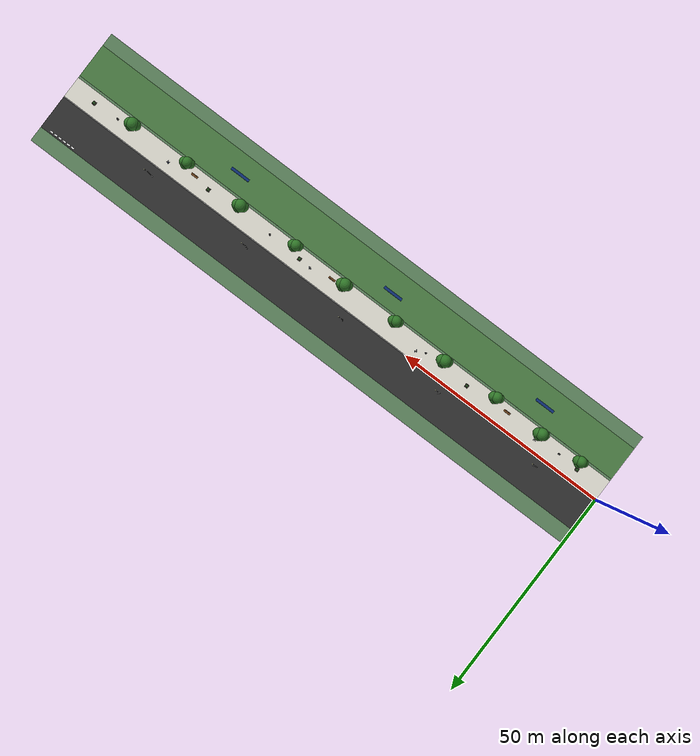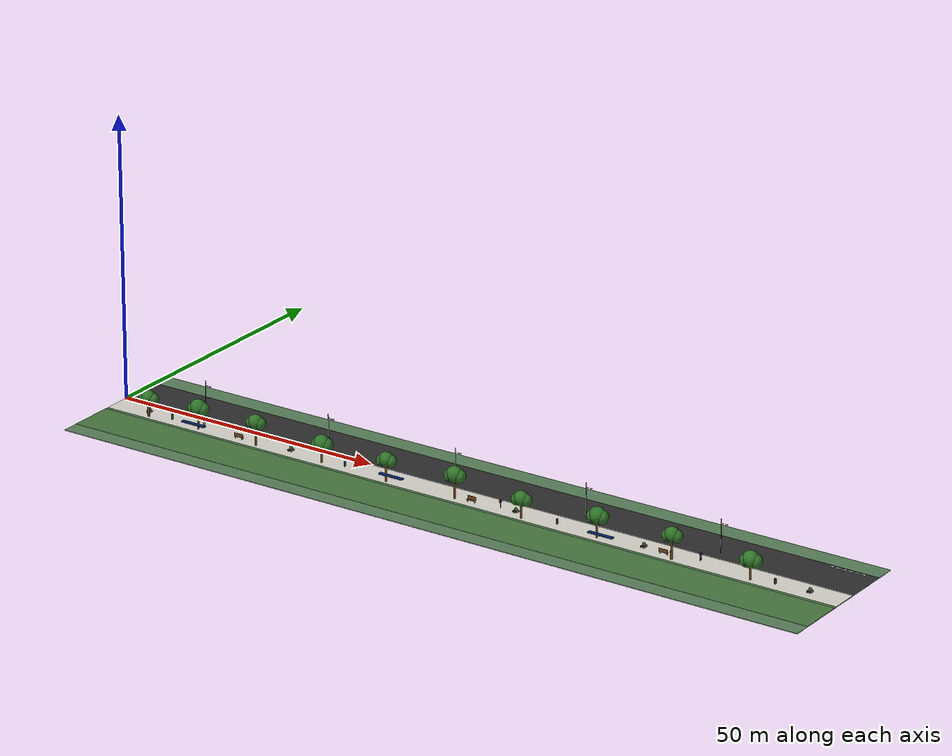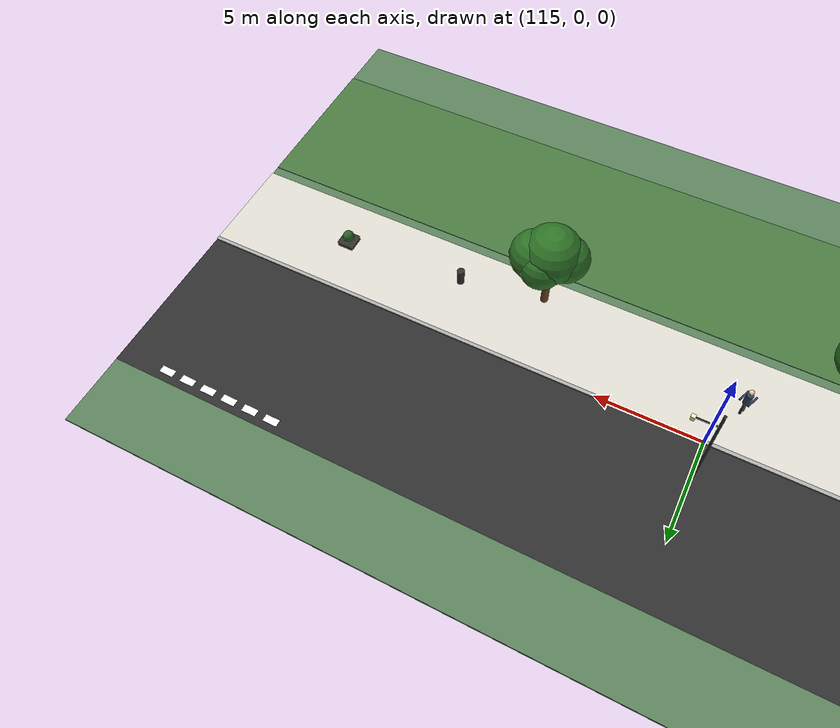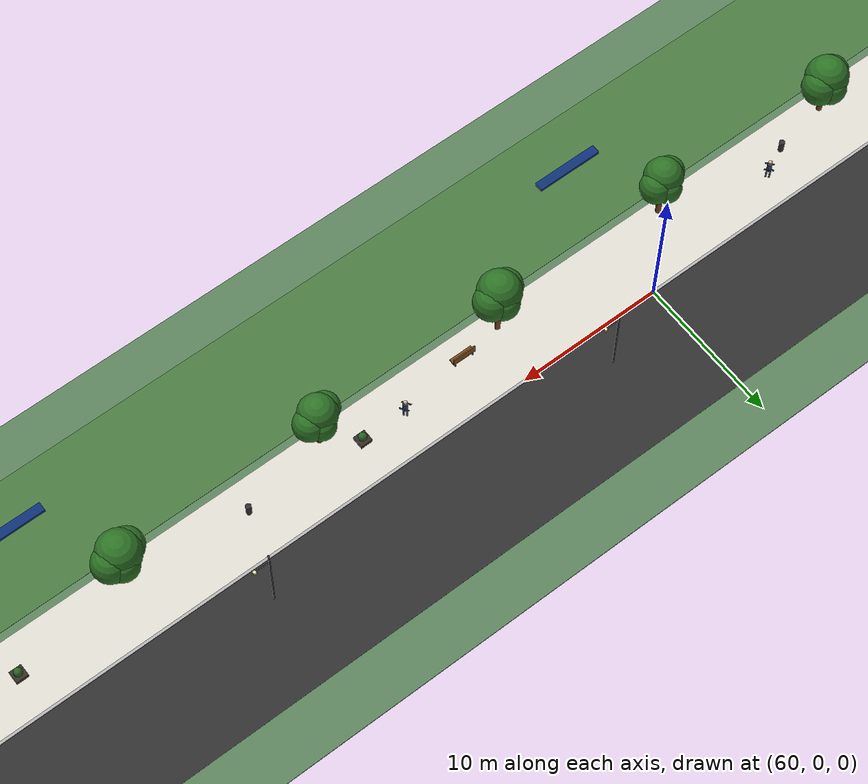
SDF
<sdf version="1.6">
  <world name="sidewalk_avenue">
    <physics name="1ms" type="ignored">
            <max_step_size>0.001</max_step_size>
            <real_time_factor>1.0</real_time_factor>
        </physics>
        <plugin filename="gz-sim-physics-system" name="gz::sim::systems::Physics"></plugin>
        <plugin filename="gz-sim-user-commands-system" name="gz::sim::systems::UserCommands"></plugin>
        <plugin filename="gz-sim-scene-broadcaster-system" name="gz::sim::systems::SceneBroadcaster"></plugin>
        <plugin filename="gz-sim-contact-system" name="gz::sim::systems::Contact"></plugin>
        <plugin filename="gz-sim-sensors-system" name="gz::sim::systems::Sensors">
            <render_engine>ogre2</render_engine>
        </plugin>
        <plugin filename="gz-sim-imu-system" name="gz::sim::systems::Imu"></plugin>

        <spherical_coordinates>
            <surface_model>EARTH_WGS84</surface_model>
            <world_frame_orientation>ENU</world_frame_orientation>
            <latitude_deg>47.478950</latitude_deg>
            <longitude_deg>19.057785</longitude_deg>
            <elevation>0</elevation>
            <heading_deg>0</heading_deg>
        </spherical_coordinates>

        <gravity>0 0 -9.8000000000000007</gravity>
        <magnetic_field>5.5644999999999998e-06 2.2875799999999999e-05 -4.2388400000000002e-05</magnetic_field>
        <atmosphere type='adiabatic'/>

        <scene>
          <ambient>0.40 0.40 0.40 1</ambient>
          <background>0.70 0.70 0.70 1</background>
          <shadows>true</shadows>
        </scene>

        <light type="directional" name="sun">
            <cast_shadows>true</cast_shadows>
            <pose>0 0 10 0 0 0</pose>
            <diffuse>0.8 0.8 0.8 1</diffuse>
            <specular>0.2 0.2 0.2 1</specular>
            <attenuation>
                <range>1000</range>
                <constant>0.9</constant>
                <linear>0.01</linear>
                <quadratic>0.001</quadratic>
            </attenuation>
            <direction>-0.5 0.1 -0.9</direction>
        </light>

    <model name="base_ground">
      <pose>70.000 -2.500 -0.050 0.000 0.000 0.000</pose>
      <static>true</static>
      <link name="link">
        <collision name="collision">
          <geometry>
            <box>
              <size>140.000 28.000 0.100</size>
            </box>
          </geometry>
        </collision>
        <visual name="visual">
          <geometry>
            <box>
              <size>140.000 28.000 0.100</size>
            </box>
          </geometry>
          <material>
            <ambient>0.280 0.400 0.280 1.000</ambient>
            <diffuse>0.350 0.500 0.350 1.000</diffuse>
            <specular>0.050 0.050 0.050 1.000</specular>
          </material>
        </visual>
      </link>
    </model>
    <model name="road_surface">
      <pose>70.000 4.000 0.001 0.000 0.000 0.000</pose>
      <static>true</static>
      <link name="link">
        <collision name="collision">
          <geometry>
            <box>
              <size>140.000 8.000 0.020</size>
            </box>
          </geometry>
        </collision>
        <visual name="visual">
          <geometry>
            <box>
              <size>140.000 8.000 0.020</size>
            </box>
          </geometry>
          <material>
            <ambient>0.144 0.144 0.144 1.000</ambient>
            <diffuse>0.180 0.180 0.180 1.000</diffuse>
            <specular>0.050 0.050 0.050 1.000</specular>
          </material>
        </visual>
      </link>      <plugin filename="gz-sim-label-system" name="gz::sim::systems::Label">
        <label>1</label>
      </plugin>
    </model>
    <model name="sidewalk_surface">
      <pose>70.000 -2.500 0.030 0.000 0.000 0.000</pose>
      <static>true</static>
      <link name="link">
        <collision name="collision">
          <geometry>
            <box>
              <size>140.000 5.000 0.060</size>
            </box>
          </geometry>
        </collision>
        <visual name="visual">
          <pose>0 0 0.030 0 0 0</pose>
          <geometry>
            <mesh>
              <uri>../meshes/sidewalk_plane.obj</uri>
            </mesh>
          </geometry>
          <material>
            <ambient>0.70 0.69 0.66 1.0</ambient>
            <diffuse>0.85 0.84 0.80 1.0</diffuse>
            <specular>0.05 0.05 0.05 1.0</specular>
            <pbr>
              <metal>
                <albedo_map>../meshes/sidewalk_diffuse.png</albedo_map>
                <metalness>0.0</metalness>
                <roughness>0.92</roughness>
              </metal>
            </pbr>
          </material>
        </visual>
      </link>      <plugin filename="gz-sim-label-system" name="gz::sim::systems::Label">
        <label>2</label>
      </plugin>
    </model>
    <model name="curb">
      <pose>70.000 0.000 0.040 0.000 0.000 0.000</pose>
      <static>true</static>
      <link name="link">
        <collision name="collision">
          <geometry>
            <box>
              <size>140.000 0.180 0.080</size>
            </box>
          </geometry>
        </collision>
        <visual name="visual">
          <geometry>
            <box>
              <size>140.000 0.180 0.080</size>
            </box>
          </geometry>
          <material>
            <ambient>0.544 0.544 0.544 1.000</ambient>
            <diffuse>0.680 0.680 0.680 1.000</diffuse>
            <specular>0.050 0.050 0.050 1.000</specular>
          </material>
        </visual>
      </link>      <plugin filename="gz-sim-label-system" name="gz::sim::systems::Label">
        <label>1</label>
      </plugin>
    </model>
    <model name="grass_strip">
      <pose>70.000 -9.500 0.015 0.000 0.000 0.000</pose>
      <static>true</static>
      <link name="link">
        <collision name="collision">
          <geometry>
            <box>
              <size>140.000 8.000 0.030</size>
            </box>
          </geometry>
        </collision>
        <visual name="visual">
          <geometry>
            <box>
              <size>140.000 8.000 0.030</size>
            </box>
          </geometry>
          <material>
            <ambient>0.224 0.376 0.200 1.000</ambient>
            <diffuse>0.280 0.470 0.250 1.000</diffuse>
            <specular>0.050 0.050 0.050 1.000</specular>
          </material>
        </visual>
      </link>      <plugin filename="gz-sim-label-system" name="gz::sim::systems::Label">
        <label>10</label>
      </plugin>
    </model>

    <model name="tree_1">
      <pose>8.000 -4.250 0.000 0.000 0.000 0.000</pose>
      <static>true</static>
      <link name="link">
        <collision name="cylinder_trunk_collision">
          <pose>0.000 0.000 1.500 0.000 0.000 0.000</pose>
          <geometry>
            <cylinder>
              <radius>0.180</radius>
              <length>3.000</length>
            </cylinder>
          </geometry>
        </collision>
        <visual name="cylinder_trunk_visual">
          <pose>0.000 0.000 1.500 0.000 0.000 0.000</pose>
          <geometry>
            <cylinder>
              <radius>0.180</radius>
              <length>3.000</length>
            </cylinder>
          </geometry>
          <material>
            <ambient>0.360 0.224 0.096 1.000</ambient>
            <diffuse>0.450 0.280 0.120 1.000</diffuse>
            <specular>0.050 0.050 0.050 1.000</specular>
          </material>
        </visual>
        <visual name="canopy_visual_0">
          <pose>0.000 0.000 3.480 0.000 0.000 0.000</pose>
          <geometry>
            <sphere>
              <radius>1.250</radius>
            </sphere>
          </geometry>
          <material>
            <ambient>0.144 0.360 0.120 1.000</ambient>
            <diffuse>0.180 0.450 0.150 1.000</diffuse>
            <specular>0.050 0.050 0.050 1.000</specular>
          </material>
        </visual>
        <visual name="canopy_visual_1">
          <pose>0.700 0.200 3.240 0.000 0.000 0.000</pose>
          <geometry>
            <sphere>
              <radius>1.062</radius>
            </sphere>
          </geometry>
          <material>
            <ambient>0.144 0.360 0.120 1.000</ambient>
            <diffuse>0.180 0.450 0.150 1.000</diffuse>
            <specular>0.050 0.050 0.050 1.000</specular>
          </material>
        </visual>
        <visual name="canopy_visual_2">
          <pose>-0.600 -0.200 3.240 0.000 0.000 0.000</pose>
          <geometry>
            <sphere>
              <radius>1.000</radius>
            </sphere>
          </geometry>
          <material>
            <ambient>0.144 0.360 0.120 1.000</ambient>
            <diffuse>0.180 0.450 0.150 1.000</diffuse>
            <specular>0.050 0.050 0.050 1.000</specular>
          </material>
        </visual>
        <visual name="canopy_visual_3">
          <pose>0.200 0.600 3.120 0.000 0.000 0.000</pose>
          <geometry>
            <sphere>
              <radius>0.938</radius>
            </sphere>
          </geometry>
          <material>
            <ambient>0.144 0.360 0.120 1.000</ambient>
            <diffuse>0.180 0.450 0.150 1.000</diffuse>
            <specular>0.050 0.050 0.050 1.000</specular>
          </material>
        </visual>
        <collision name="canopy_collision">
          <pose>0.000 0.000 3.360 0.000 0.000 0.000</pose>
          <geometry>
            <sphere>
              <radius>1.500</radius>
            </sphere>
          </geometry>
        </collision>
      </link>      <plugin filename="gz-sim-label-system" name="gz::sim::systems::Label">
        <label>9</label>
      </plugin>
    </model>
    <model name="tree_2">
      <pose>18.000 -3.850 0.000 0.000 0.000 0.000</pose>
      <static>true</static>
      <link name="link">
        <collision name="cylinder_trunk_collision">
          <pose>0.000 0.000 1.700 0.000 0.000 0.000</pose>
          <geometry>
            <cylinder>
              <radius>0.180</radius>
              <length>3.400</length>
            </cylinder>
          </geometry>
        </collision>
        <visual name="cylinder_trunk_visual">
          <pose>0.000 0.000 1.700 0.000 0.000 0.000</pose>
          <geometry>
            <cylinder>
              <radius>0.180</radius>
              <length>3.400</length>
            </cylinder>
          </geometry>
          <material>
            <ambient>0.360 0.224 0.096 1.000</ambient>
            <diffuse>0.450 0.280 0.120 1.000</diffuse>
            <specular>0.050 0.050 0.050 1.000</specular>
          </material>
        </visual>
        <visual name="canopy_visual_0">
          <pose>0.000 0.000 3.880 0.000 0.000 0.000</pose>
          <geometry>
            <sphere>
              <radius>1.400</radius>
            </sphere>
          </geometry>
          <material>
            <ambient>0.144 0.360 0.120 1.000</ambient>
            <diffuse>0.180 0.450 0.150 1.000</diffuse>
            <specular>0.050 0.050 0.050 1.000</specular>
          </material>
        </visual>
        <visual name="canopy_visual_1">
          <pose>0.700 0.200 3.640 0.000 0.000 0.000</pose>
          <geometry>
            <sphere>
              <radius>1.190</radius>
            </sphere>
          </geometry>
          <material>
            <ambient>0.144 0.360 0.120 1.000</ambient>
            <diffuse>0.180 0.450 0.150 1.000</diffuse>
            <specular>0.050 0.050 0.050 1.000</specular>
          </material>
        </visual>
        <visual name="canopy_visual_2">
          <pose>-0.600 -0.200 3.640 0.000 0.000 0.000</pose>
          <geometry>
            <sphere>
              <radius>1.120</radius>
            </sphere>
          </geometry>
          <material>
            <ambient>0.144 0.360 0.120 1.000</ambient>
            <diffuse>0.180 0.450 0.150 1.000</diffuse>
            <specular>0.050 0.050 0.050 1.000</specular>
          </material>
        </visual>
        <visual name="canopy_visual_3">
          <pose>0.200 0.600 3.520 0.000 0.000 0.000</pose>
          <geometry>
            <sphere>
              <radius>1.050</radius>
            </sphere>
          </geometry>
          <material>
            <ambient>0.144 0.360 0.120 1.000</ambient>
            <diffuse>0.180 0.450 0.150 1.000</diffuse>
            <specular>0.050 0.050 0.050 1.000</specular>
          </material>
        </visual>
        <collision name="canopy_collision">
          <pose>0.000 0.000 3.760 0.000 0.000 0.000</pose>
          <geometry>
            <sphere>
              <radius>1.680</radius>
            </sphere>
          </geometry>
        </collision>
      </link>      <plugin filename="gz-sim-label-system" name="gz::sim::systems::Label">
        <label>9</label>
      </plugin>
    </model>
    <model name="tree_3">
      <pose>30.000 -4.250 0.000 0.000 0.000 0.000</pose>
      <static>true</static>
      <link name="link">
        <collision name="cylinder_trunk_collision">
          <pose>0.000 0.000 1.900 0.000 0.000 0.000</pose>
          <geometry>
            <cylinder>
              <radius>0.180</radius>
              <length>3.800</length>
            </cylinder>
          </geometry>
        </collision>
        <visual name="cylinder_trunk_visual">
          <pose>0.000 0.000 1.900 0.000 0.000 0.000</pose>
          <geometry>
            <cylinder>
              <radius>0.180</radius>
              <length>3.800</length>
            </cylinder>
          </geometry>
          <material>
            <ambient>0.360 0.224 0.096 1.000</ambient>
            <diffuse>0.450 0.280 0.120 1.000</diffuse>
            <specular>0.050 0.050 0.050 1.000</specular>
          </material>
        </visual>
        <visual name="canopy_visual_0">
          <pose>0.000 0.000 4.280 0.000 0.000 0.000</pose>
          <geometry>
            <sphere>
              <radius>1.250</radius>
            </sphere>
          </geometry>
          <material>
            <ambient>0.144 0.360 0.120 1.000</ambient>
            <diffuse>0.180 0.450 0.150 1.000</diffuse>
            <specular>0.050 0.050 0.050 1.000</specular>
          </material>
        </visual>
        <visual name="canopy_visual_1">
          <pose>0.700 0.200 4.040 0.000 0.000 0.000</pose>
          <geometry>
            <sphere>
              <radius>1.062</radius>
            </sphere>
          </geometry>
          <material>
            <ambient>0.144 0.360 0.120 1.000</ambient>
            <diffuse>0.180 0.450 0.150 1.000</diffuse>
            <specular>0.050 0.050 0.050 1.000</specular>
          </material>
        </visual>
        <visual name="canopy_visual_2">
          <pose>-0.600 -0.200 4.040 0.000 0.000 0.000</pose>
          <geometry>
            <sphere>
              <radius>1.000</radius>
            </sphere>
          </geometry>
          <material>
            <ambient>0.144 0.360 0.120 1.000</ambient>
            <diffuse>0.180 0.450 0.150 1.000</diffuse>
            <specular>0.050 0.050 0.050 1.000</specular>
          </material>
        </visual>
        <visual name="canopy_visual_3">
          <pose>0.200 0.600 3.920 0.000 0.000 0.000</pose>
          <geometry>
            <sphere>
              <radius>0.938</radius>
            </sphere>
          </geometry>
          <material>
            <ambient>0.144 0.360 0.120 1.000</ambient>
            <diffuse>0.180 0.450 0.150 1.000</diffuse>
            <specular>0.050 0.050 0.050 1.000</specular>
          </material>
        </visual>
        <collision name="canopy_collision">
          <pose>0.000 0.000 4.160 0.000 0.000 0.000</pose>
          <geometry>
            <sphere>
              <radius>1.500</radius>
            </sphere>
          </geometry>
        </collision>
      </link>      <plugin filename="gz-sim-label-system" name="gz::sim::systems::Label">
        <label>9</label>
      </plugin>
    </model>
    <model name="tree_4">
      <pose>43.000 -3.850 0.000 0.000 0.000 0.000</pose>
      <static>true</static>
      <link name="link">
        <collision name="cylinder_trunk_collision">
          <pose>0.000 0.000 1.500 0.000 0.000 0.000</pose>
          <geometry>
            <cylinder>
              <radius>0.180</radius>
              <length>3.000</length>
            </cylinder>
          </geometry>
        </collision>
        <visual name="cylinder_trunk_visual">
          <pose>0.000 0.000 1.500 0.000 0.000 0.000</pose>
          <geometry>
            <cylinder>
              <radius>0.180</radius>
              <length>3.000</length>
            </cylinder>
          </geometry>
          <material>
            <ambient>0.360 0.224 0.096 1.000</ambient>
            <diffuse>0.450 0.280 0.120 1.000</diffuse>
            <specular>0.050 0.050 0.050 1.000</specular>
          </material>
        </visual>
        <visual name="canopy_visual_0">
          <pose>0.000 0.000 3.480 0.000 0.000 0.000</pose>
          <geometry>
            <sphere>
              <radius>1.400</radius>
            </sphere>
          </geometry>
          <material>
            <ambient>0.144 0.360 0.120 1.000</ambient>
            <diffuse>0.180 0.450 0.150 1.000</diffuse>
            <specular>0.050 0.050 0.050 1.000</specular>
          </material>
        </visual>
        <visual name="canopy_visual_1">
          <pose>0.700 0.200 3.240 0.000 0.000 0.000</pose>
          <geometry>
            <sphere>
              <radius>1.190</radius>
            </sphere>
          </geometry>
          <material>
            <ambient>0.144 0.360 0.120 1.000</ambient>
            <diffuse>0.180 0.450 0.150 1.000</diffuse>
            <specular>0.050 0.050 0.050 1.000</specular>
          </material>
        </visual>
        <visual name="canopy_visual_2">
          <pose>-0.600 -0.200 3.240 0.000 0.000 0.000</pose>
          <geometry>
            <sphere>
              <radius>1.120</radius>
            </sphere>
          </geometry>
          <material>
            <ambient>0.144 0.360 0.120 1.000</ambient>
            <diffuse>0.180 0.450 0.150 1.000</diffuse>
            <specular>0.050 0.050 0.050 1.000</specular>
          </material>
        </visual>
        <visual name="canopy_visual_3">
          <pose>0.200 0.600 3.120 0.000 0.000 0.000</pose>
          <geometry>
            <sphere>
              <radius>1.050</radius>
            </sphere>
          </geometry>
          <material>
            <ambient>0.144 0.360 0.120 1.000</ambient>
            <diffuse>0.180 0.450 0.150 1.000</diffuse>
            <specular>0.050 0.050 0.050 1.000</specular>
          </material>
        </visual>
        <collision name="canopy_collision">
          <pose>0.000 0.000 3.360 0.000 0.000 0.000</pose>
          <geometry>
            <sphere>
              <radius>1.680</radius>
            </sphere>
          </geometry>
        </collision>
      </link>      <plugin filename="gz-sim-label-system" name="gz::sim::systems::Label">
        <label>9</label>
      </plugin>
    </model>
    <model name="tree_5">
      <pose>56.000 -4.250 0.000 0.000 0.000 0.000</pose>
      <static>true</static>
      <link name="link">
        <collision name="cylinder_trunk_collision">
          <pose>0.000 0.000 1.700 0.000 0.000 0.000</pose>
          <geometry>
            <cylinder>
              <radius>0.180</radius>
              <length>3.400</length>
            </cylinder>
          </geometry>
        </collision>
        <visual name="cylinder_trunk_visual">
          <pose>0.000 0.000 1.700 0.000 0.000 0.000</pose>
          <geometry>
            <cylinder>
              <radius>0.180</radius>
              <length>3.400</length>
            </cylinder>
          </geometry>
          <material>
            <ambient>0.360 0.224 0.096 1.000</ambient>
            <diffuse>0.450 0.280 0.120 1.000</diffuse>
            <specular>0.050 0.050 0.050 1.000</specular>
          </material>
        </visual>
        <visual name="canopy_visual_0">
          <pose>0.000 0.000 3.880 0.000 0.000 0.000</pose>
          <geometry>
            <sphere>
              <radius>1.250</radius>
            </sphere>
          </geometry>
          <material>
            <ambient>0.144 0.360 0.120 1.000</ambient>
            <diffuse>0.180 0.450 0.150 1.000</diffuse>
            <specular>0.050 0.050 0.050 1.000</specular>
          </material>
        </visual>
        <visual name="canopy_visual_1">
          <pose>0.700 0.200 3.640 0.000 0.000 0.000</pose>
          <geometry>
            <sphere>
              <radius>1.062</radius>
            </sphere>
          </geometry>
          <material>
            <ambient>0.144 0.360 0.120 1.000</ambient>
            <diffuse>0.180 0.450 0.150 1.000</diffuse>
            <specular>0.050 0.050 0.050 1.000</specular>
          </material>
        </visual>
        <visual name="canopy_visual_2">
          <pose>-0.600 -0.200 3.640 0.000 0.000 0.000</pose>
          <geometry>
            <sphere>
              <radius>1.000</radius>
            </sphere>
          </geometry>
          <material>
            <ambient>0.144 0.360 0.120 1.000</ambient>
            <diffuse>0.180 0.450 0.150 1.000</diffuse>
            <specular>0.050 0.050 0.050 1.000</specular>
          </material>
        </visual>
        <visual name="canopy_visual_3">
          <pose>0.200 0.600 3.520 0.000 0.000 0.000</pose>
          <geometry>
            <sphere>
              <radius>0.938</radius>
            </sphere>
          </geometry>
          <material>
            <ambient>0.144 0.360 0.120 1.000</ambient>
            <diffuse>0.180 0.450 0.150 1.000</diffuse>
            <specular>0.050 0.050 0.050 1.000</specular>
          </material>
        </visual>
        <collision name="canopy_collision">
          <pose>0.000 0.000 3.760 0.000 0.000 0.000</pose>
          <geometry>
            <sphere>
              <radius>1.500</radius>
            </sphere>
          </geometry>
        </collision>
      </link>      <plugin filename="gz-sim-label-system" name="gz::sim::systems::Label">
        <label>9</label>
      </plugin>
    </model>
    <model name="tree_6">
      <pose>69.000 -3.850 0.000 0.000 0.000 0.000</pose>
      <static>true</static>
      <link name="link">
        <collision name="cylinder_trunk_collision">
          <pose>0.000 0.000 1.900 0.000 0.000 0.000</pose>
          <geometry>
            <cylinder>
              <radius>0.180</radius>
              <length>3.800</length>
            </cylinder>
          </geometry>
        </collision>
        <visual name="cylinder_trunk_visual">
          <pose>0.000 0.000 1.900 0.000 0.000 0.000</pose>
          <geometry>
            <cylinder>
              <radius>0.180</radius>
              <length>3.800</length>
            </cylinder>
          </geometry>
          <material>
            <ambient>0.360 0.224 0.096 1.000</ambient>
            <diffuse>0.450 0.280 0.120 1.000</diffuse>
            <specular>0.050 0.050 0.050 1.000</specular>
          </material>
        </visual>
        <visual name="canopy_visual_0">
          <pose>0.000 0.000 4.280 0.000 0.000 0.000</pose>
          <geometry>
            <sphere>
              <radius>1.400</radius>
            </sphere>
          </geometry>
          <material>
            <ambient>0.144 0.360 0.120 1.000</ambient>
            <diffuse>0.180 0.450 0.150 1.000</diffuse>
            <specular>0.050 0.050 0.050 1.000</specular>
          </material>
        </visual>
        <visual name="canopy_visual_1">
          <pose>0.700 0.200 4.040 0.000 0.000 0.000</pose>
          <geometry>
            <sphere>
              <radius>1.190</radius>
            </sphere>
          </geometry>
          <material>
            <ambient>0.144 0.360 0.120 1.000</ambient>
            <diffuse>0.180 0.450 0.150 1.000</diffuse>
            <specular>0.050 0.050 0.050 1.000</specular>
          </material>
        </visual>
        <visual name="canopy_visual_2">
          <pose>-0.600 -0.200 4.040 0.000 0.000 0.000</pose>
          <geometry>
            <sphere>
              <radius>1.120</radius>
            </sphere>
          </geometry>
          <material>
            <ambient>0.144 0.360 0.120 1.000</ambient>
            <diffuse>0.180 0.450 0.150 1.000</diffuse>
            <specular>0.050 0.050 0.050 1.000</specular>
          </material>
        </visual>
        <visual name="canopy_visual_3">
          <pose>0.200 0.600 3.920 0.000 0.000 0.000</pose>
          <geometry>
            <sphere>
              <radius>1.050</radius>
            </sphere>
          </geometry>
          <material>
            <ambient>0.144 0.360 0.120 1.000</ambient>
            <diffuse>0.180 0.450 0.150 1.000</diffuse>
            <specular>0.050 0.050 0.050 1.000</specular>
          </material>
        </visual>
        <collision name="canopy_collision">
          <pose>0.000 0.000 4.160 0.000 0.000 0.000</pose>
          <geometry>
            <sphere>
              <radius>1.680</radius>
            </sphere>
          </geometry>
        </collision>
      </link>      <plugin filename="gz-sim-label-system" name="gz::sim::systems::Label">
        <label>9</label>
      </plugin>
    </model>
    <model name="tree_7">
      <pose>82.000 -4.250 0.000 0.000 0.000 0.000</pose>
      <static>true</static>
      <link name="link">
        <collision name="cylinder_trunk_collision">
          <pose>0.000 0.000 1.500 0.000 0.000 0.000</pose>
          <geometry>
            <cylinder>
              <radius>0.180</radius>
              <length>3.000</length>
            </cylinder>
          </geometry>
        </collision>
        <visual name="cylinder_trunk_visual">
          <pose>0.000 0.000 1.500 0.000 0.000 0.000</pose>
          <geometry>
            <cylinder>
              <radius>0.180</radius>
              <length>3.000</length>
            </cylinder>
          </geometry>
          <material>
            <ambient>0.360 0.224 0.096 1.000</ambient>
            <diffuse>0.450 0.280 0.120 1.000</diffuse>
            <specular>0.050 0.050 0.050 1.000</specular>
          </material>
        </visual>
        <visual name="canopy_visual_0">
          <pose>0.000 0.000 3.480 0.000 0.000 0.000</pose>
          <geometry>
            <sphere>
              <radius>1.250</radius>
            </sphere>
          </geometry>
          <material>
            <ambient>0.144 0.360 0.120 1.000</ambient>
            <diffuse>0.180 0.450 0.150 1.000</diffuse>
            <specular>0.050 0.050 0.050 1.000</specular>
          </material>
        </visual>
        <visual name="canopy_visual_1">
          <pose>0.700 0.200 3.240 0.000 0.000 0.000</pose>
          <geometry>
            <sphere>
              <radius>1.062</radius>
            </sphere>
          </geometry>
          <material>
            <ambient>0.144 0.360 0.120 1.000</ambient>
            <diffuse>0.180 0.450 0.150 1.000</diffuse>
            <specular>0.050 0.050 0.050 1.000</specular>
          </material>
        </visual>
        <visual name="canopy_visual_2">
          <pose>-0.600 -0.200 3.240 0.000 0.000 0.000</pose>
          <geometry>
            <sphere>
              <radius>1.000</radius>
            </sphere>
          </geometry>
          <material>
            <ambient>0.144 0.360 0.120 1.000</ambient>
            <diffuse>0.180 0.450 0.150 1.000</diffuse>
            <specular>0.050 0.050 0.050 1.000</specular>
          </material>
        </visual>
        <visual name="canopy_visual_3">
          <pose>0.200 0.600 3.120 0.000 0.000 0.000</pose>
          <geometry>
            <sphere>
              <radius>0.938</radius>
            </sphere>
          </geometry>
          <material>
            <ambient>0.144 0.360 0.120 1.000</ambient>
            <diffuse>0.180 0.450 0.150 1.000</diffuse>
            <specular>0.050 0.050 0.050 1.000</specular>
          </material>
        </visual>
        <collision name="canopy_collision">
          <pose>0.000 0.000 3.360 0.000 0.000 0.000</pose>
          <geometry>
            <sphere>
              <radius>1.500</radius>
            </sphere>
          </geometry>
        </collision>
      </link>      <plugin filename="gz-sim-label-system" name="gz::sim::systems::Label">
        <label>9</label>
      </plugin>
    </model>
    <model name="tree_8">
      <pose>96.000 -3.850 0.000 0.000 0.000 0.000</pose>
      <static>true</static>
      <link name="link">
        <collision name="cylinder_trunk_collision">
          <pose>0.000 0.000 1.700 0.000 0.000 0.000</pose>
          <geometry>
            <cylinder>
              <radius>0.180</radius>
              <length>3.400</length>
            </cylinder>
          </geometry>
        </collision>
        <visual name="cylinder_trunk_visual">
          <pose>0.000 0.000 1.700 0.000 0.000 0.000</pose>
          <geometry>
            <cylinder>
              <radius>0.180</radius>
              <length>3.400</length>
            </cylinder>
          </geometry>
          <material>
            <ambient>0.360 0.224 0.096 1.000</ambient>
            <diffuse>0.450 0.280 0.120 1.000</diffuse>
            <specular>0.050 0.050 0.050 1.000</specular>
          </material>
        </visual>
        <visual name="canopy_visual_0">
          <pose>0.000 0.000 3.880 0.000 0.000 0.000</pose>
          <geometry>
            <sphere>
              <radius>1.400</radius>
            </sphere>
          </geometry>
          <material>
            <ambient>0.144 0.360 0.120 1.000</ambient>
            <diffuse>0.180 0.450 0.150 1.000</diffuse>
            <specular>0.050 0.050 0.050 1.000</specular>
          </material>
        </visual>
        <visual name="canopy_visual_1">
          <pose>0.700 0.200 3.640 0.000 0.000 0.000</pose>
          <geometry>
            <sphere>
              <radius>1.190</radius>
            </sphere>
          </geometry>
          <material>
            <ambient>0.144 0.360 0.120 1.000</ambient>
            <diffuse>0.180 0.450 0.150 1.000</diffuse>
            <specular>0.050 0.050 0.050 1.000</specular>
          </material>
        </visual>
        <visual name="canopy_visual_2">
          <pose>-0.600 -0.200 3.640 0.000 0.000 0.000</pose>
          <geometry>
            <sphere>
              <radius>1.120</radius>
            </sphere>
          </geometry>
          <material>
            <ambient>0.144 0.360 0.120 1.000</ambient>
            <diffuse>0.180 0.450 0.150 1.000</diffuse>
            <specular>0.050 0.050 0.050 1.000</specular>
          </material>
        </visual>
        <visual name="canopy_visual_3">
          <pose>0.200 0.600 3.520 0.000 0.000 0.000</pose>
          <geometry>
            <sphere>
              <radius>1.050</radius>
            </sphere>
          </geometry>
          <material>
            <ambient>0.144 0.360 0.120 1.000</ambient>
            <diffuse>0.180 0.450 0.150 1.000</diffuse>
            <specular>0.050 0.050 0.050 1.000</specular>
          </material>
        </visual>
        <collision name="canopy_collision">
          <pose>0.000 0.000 3.760 0.000 0.000 0.000</pose>
          <geometry>
            <sphere>
              <radius>1.680</radius>
            </sphere>
          </geometry>
        </collision>
      </link>      <plugin filename="gz-sim-label-system" name="gz::sim::systems::Label">
        <label>9</label>
      </plugin>
    </model>
    <model name="tree_9">
      <pose>110.000 -4.250 0.000 0.000 0.000 0.000</pose>
      <static>true</static>
      <link name="link">
        <collision name="cylinder_trunk_collision">
          <pose>0.000 0.000 1.900 0.000 0.000 0.000</pose>
          <geometry>
            <cylinder>
              <radius>0.180</radius>
              <length>3.800</length>
            </cylinder>
          </geometry>
        </collision>
        <visual name="cylinder_trunk_visual">
          <pose>0.000 0.000 1.900 0.000 0.000 0.000</pose>
          <geometry>
            <cylinder>
              <radius>0.180</radius>
              <length>3.800</length>
            </cylinder>
          </geometry>
          <material>
            <ambient>0.360 0.224 0.096 1.000</ambient>
            <diffuse>0.450 0.280 0.120 1.000</diffuse>
            <specular>0.050 0.050 0.050 1.000</specular>
          </material>
        </visual>
        <visual name="canopy_visual_0">
          <pose>0.000 0.000 4.280 0.000 0.000 0.000</pose>
          <geometry>
            <sphere>
              <radius>1.250</radius>
            </sphere>
          </geometry>
          <material>
            <ambient>0.144 0.360 0.120 1.000</ambient>
            <diffuse>0.180 0.450 0.150 1.000</diffuse>
            <specular>0.050 0.050 0.050 1.000</specular>
          </material>
        </visual>
        <visual name="canopy_visual_1">
          <pose>0.700 0.200 4.040 0.000 0.000 0.000</pose>
          <geometry>
            <sphere>
              <radius>1.062</radius>
            </sphere>
          </geometry>
          <material>
            <ambient>0.144 0.360 0.120 1.000</ambient>
            <diffuse>0.180 0.450 0.150 1.000</diffuse>
            <specular>0.050 0.050 0.050 1.000</specular>
          </material>
        </visual>
        <visual name="canopy_visual_2">
          <pose>-0.600 -0.200 4.040 0.000 0.000 0.000</pose>
          <geometry>
            <sphere>
              <radius>1.000</radius>
            </sphere>
          </geometry>
          <material>
            <ambient>0.144 0.360 0.120 1.000</ambient>
            <diffuse>0.180 0.450 0.150 1.000</diffuse>
            <specular>0.050 0.050 0.050 1.000</specular>
          </material>
        </visual>
        <visual name="canopy_visual_3">
          <pose>0.200 0.600 3.920 0.000 0.000 0.000</pose>
          <geometry>
            <sphere>
              <radius>0.938</radius>
            </sphere>
          </geometry>
          <material>
            <ambient>0.144 0.360 0.120 1.000</ambient>
            <diffuse>0.180 0.450 0.150 1.000</diffuse>
            <specular>0.050 0.050 0.050 1.000</specular>
          </material>
        </visual>
        <collision name="canopy_collision">
          <pose>0.000 0.000 4.160 0.000 0.000 0.000</pose>
          <geometry>
            <sphere>
              <radius>1.500</radius>
            </sphere>
          </geometry>
        </collision>
      </link>      <plugin filename="gz-sim-label-system" name="gz::sim::systems::Label">
        <label>9</label>
      </plugin>
    </model>
    <model name="tree_10">
      <pose>124.000 -3.850 0.000 0.000 0.000 0.000</pose>
      <static>true</static>
      <link name="link">
        <collision name="cylinder_trunk_collision">
          <pose>0.000 0.000 1.500 0.000 0.000 0.000</pose>
          <geometry>
            <cylinder>
              <radius>0.180</radius>
              <length>3.000</length>
            </cylinder>
          </geometry>
        </collision>
        <visual name="cylinder_trunk_visual">
          <pose>0.000 0.000 1.500 0.000 0.000 0.000</pose>
          <geometry>
            <cylinder>
              <radius>0.180</radius>
              <length>3.000</length>
            </cylinder>
          </geometry>
          <material>
            <ambient>0.360 0.224 0.096 1.000</ambient>
            <diffuse>0.450 0.280 0.120 1.000</diffuse>
            <specular>0.050 0.050 0.050 1.000</specular>
          </material>
        </visual>
        <visual name="canopy_visual_0">
          <pose>0.000 0.000 3.480 0.000 0.000 0.000</pose>
          <geometry>
            <sphere>
              <radius>1.400</radius>
            </sphere>
          </geometry>
          <material>
            <ambient>0.144 0.360 0.120 1.000</ambient>
            <diffuse>0.180 0.450 0.150 1.000</diffuse>
            <specular>0.050 0.050 0.050 1.000</specular>
          </material>
        </visual>
        <visual name="canopy_visual_1">
          <pose>0.700 0.200 3.240 0.000 0.000 0.000</pose>
          <geometry>
            <sphere>
              <radius>1.190</radius>
            </sphere>
          </geometry>
          <material>
            <ambient>0.144 0.360 0.120 1.000</ambient>
            <diffuse>0.180 0.450 0.150 1.000</diffuse>
            <specular>0.050 0.050 0.050 1.000</specular>
          </material>
        </visual>
        <visual name="canopy_visual_2">
          <pose>-0.600 -0.200 3.240 0.000 0.000 0.000</pose>
          <geometry>
            <sphere>
              <radius>1.120</radius>
            </sphere>
          </geometry>
          <material>
            <ambient>0.144 0.360 0.120 1.000</ambient>
            <diffuse>0.180 0.450 0.150 1.000</diffuse>
            <specular>0.050 0.050 0.050 1.000</specular>
          </material>
        </visual>
        <visual name="canopy_visual_3">
          <pose>0.200 0.600 3.120 0.000 0.000 0.000</pose>
          <geometry>
            <sphere>
              <radius>1.050</radius>
            </sphere>
          </geometry>
          <material>
            <ambient>0.144 0.360 0.120 1.000</ambient>
            <diffuse>0.180 0.450 0.150 1.000</diffuse>
            <specular>0.050 0.050 0.050 1.000</specular>
          </material>
        </visual>
        <collision name="canopy_collision">
          <pose>0.000 0.000 3.360 0.000 0.000 0.000</pose>
          <geometry>
            <sphere>
              <radius>1.680</radius>
            </sphere>
          </geometry>
        </collision>
      </link>      <plugin filename="gz-sim-label-system" name="gz::sim::systems::Label">
        <label>9</label>
      </plugin>
    </model>
    <model name="lamp_1">
      <pose>15.000 2.200 0.000 0.000 0.000 0.000</pose>
      <static>true</static>
      <link name="link">
        <collision name="pole_collision">
          <pose>0.000 0.000 2.900 0.000 0.000 0.000</pose>
          <geometry>
            <cylinder>
              <radius>0.060</radius>
              <length>5.800</length>
            </cylinder>
          </geometry>
        </collision>
        <visual name="pole_visual">
          <pose>0.000 0.000 2.900 0.000 0.000 0.000</pose>
          <geometry>
            <cylinder>
              <radius>0.060</radius>
              <length>5.800</length>
            </cylinder>
          </geometry>
          <material>
            <ambient>0.120 0.120 0.120 1.000</ambient>
            <diffuse>0.150 0.150 0.150 1.000</diffuse>
            <specular>0.050 0.050 0.050 1.000</specular>
          </material>
        </visual>
        <visual name="arm_visual">
          <pose>0.550 0.000 5.000 0.000 0.000 0.000</pose>
          <geometry>
            <box>
              <size>1.100 0.050 0.050</size>
            </box>
          </geometry>
          <material>
            <ambient>0.120 0.120 0.120 1.000</ambient>
            <diffuse>0.150 0.150 0.150 1.000</diffuse>
            <specular>0.050 0.050 0.050 1.000</specular>
          </material>
        </visual>
        <visual name="lamp_visual">
          <pose>1.000 0.000 4.950 0.000 0.000 0.000</pose>
          <geometry>
            <box>
              <size>0.180 0.180 0.220</size>
            </box>
          </geometry>
          <material>
            <ambient>0.760 0.760 0.560 1.000</ambient>
            <diffuse>0.950 0.950 0.700 1.000</diffuse>
            <specular>0.050 0.050 0.050 1.000</specular>
          </material>
        </visual>
      </link>      <plugin filename="gz-sim-label-system" name="gz::sim::systems::Label">
        <label>6</label>
      </plugin>
    </model>
    <model name="lamp_2">
      <pose>40.000 2.200 0.000 0.000 0.000 0.000</pose>
      <static>true</static>
      <link name="link">
        <collision name="pole_collision">
          <pose>0.000 0.000 2.900 0.000 0.000 0.000</pose>
          <geometry>
            <cylinder>
              <radius>0.060</radius>
              <length>5.800</length>
            </cylinder>
          </geometry>
        </collision>
        <visual name="pole_visual">
          <pose>0.000 0.000 2.900 0.000 0.000 0.000</pose>
          <geometry>
            <cylinder>
              <radius>0.060</radius>
              <length>5.800</length>
            </cylinder>
          </geometry>
          <material>
            <ambient>0.120 0.120 0.120 1.000</ambient>
            <diffuse>0.150 0.150 0.150 1.000</diffuse>
            <specular>0.050 0.050 0.050 1.000</specular>
          </material>
        </visual>
        <visual name="arm_visual">
          <pose>0.550 0.000 5.000 0.000 0.000 0.000</pose>
          <geometry>
            <box>
              <size>1.100 0.050 0.050</size>
            </box>
          </geometry>
          <material>
            <ambient>0.120 0.120 0.120 1.000</ambient>
            <diffuse>0.150 0.150 0.150 1.000</diffuse>
            <specular>0.050 0.050 0.050 1.000</specular>
          </material>
        </visual>
        <visual name="lamp_visual">
          <pose>1.000 0.000 4.950 0.000 0.000 0.000</pose>
          <geometry>
            <box>
              <size>0.180 0.180 0.220</size>
            </box>
          </geometry>
          <material>
            <ambient>0.760 0.760 0.560 1.000</ambient>
            <diffuse>0.950 0.950 0.700 1.000</diffuse>
            <specular>0.050 0.050 0.050 1.000</specular>
          </material>
        </visual>
      </link>      <plugin filename="gz-sim-label-system" name="gz::sim::systems::Label">
        <label>6</label>
      </plugin>
    </model>
    <model name="lamp_3">
      <pose>65.000 2.200 0.000 0.000 0.000 0.000</pose>
      <static>true</static>
      <link name="link">
        <collision name="pole_collision">
          <pose>0.000 0.000 2.900 0.000 0.000 0.000</pose>
          <geometry>
            <cylinder>
              <radius>0.060</radius>
              <length>5.800</length>
            </cylinder>
          </geometry>
        </collision>
        <visual name="pole_visual">
          <pose>0.000 0.000 2.900 0.000 0.000 0.000</pose>
          <geometry>
            <cylinder>
              <radius>0.060</radius>
              <length>5.800</length>
            </cylinder>
          </geometry>
          <material>
            <ambient>0.120 0.120 0.120 1.000</ambient>
            <diffuse>0.150 0.150 0.150 1.000</diffuse>
            <specular>0.050 0.050 0.050 1.000</specular>
          </material>
        </visual>
        <visual name="arm_visual">
          <pose>0.550 0.000 5.000 0.000 0.000 0.000</pose>
          <geometry>
            <box>
              <size>1.100 0.050 0.050</size>
            </box>
          </geometry>
          <material>
            <ambient>0.120 0.120 0.120 1.000</ambient>
            <diffuse>0.150 0.150 0.150 1.000</diffuse>
            <specular>0.050 0.050 0.050 1.000</specular>
          </material>
        </visual>
        <visual name="lamp_visual">
          <pose>1.000 0.000 4.950 0.000 0.000 0.000</pose>
          <geometry>
            <box>
              <size>0.180 0.180 0.220</size>
            </box>
          </geometry>
          <material>
            <ambient>0.760 0.760 0.560 1.000</ambient>
            <diffuse>0.950 0.950 0.700 1.000</diffuse>
            <specular>0.050 0.050 0.050 1.000</specular>
          </material>
        </visual>
      </link>      <plugin filename="gz-sim-label-system" name="gz::sim::systems::Label">
        <label>6</label>
      </plugin>
    </model>
    <model name="lamp_4">
      <pose>90.000 2.200 0.000 0.000 0.000 0.000</pose>
      <static>true</static>
      <link name="link">
        <collision name="pole_collision">
          <pose>0.000 0.000 2.900 0.000 0.000 0.000</pose>
          <geometry>
            <cylinder>
              <radius>0.060</radius>
              <length>5.800</length>
            </cylinder>
          </geometry>
        </collision>
        <visual name="pole_visual">
          <pose>0.000 0.000 2.900 0.000 0.000 0.000</pose>
          <geometry>
            <cylinder>
              <radius>0.060</radius>
              <length>5.800</length>
            </cylinder>
          </geometry>
          <material>
            <ambient>0.120 0.120 0.120 1.000</ambient>
            <diffuse>0.150 0.150 0.150 1.000</diffuse>
            <specular>0.050 0.050 0.050 1.000</specular>
          </material>
        </visual>
        <visual name="arm_visual">
          <pose>0.550 0.000 5.000 0.000 0.000 0.000</pose>
          <geometry>
            <box>
              <size>1.100 0.050 0.050</size>
            </box>
          </geometry>
          <material>
            <ambient>0.120 0.120 0.120 1.000</ambient>
            <diffuse>0.150 0.150 0.150 1.000</diffuse>
            <specular>0.050 0.050 0.050 1.000</specular>
          </material>
        </visual>
        <visual name="lamp_visual">
          <pose>1.000 0.000 4.950 0.000 0.000 0.000</pose>
          <geometry>
            <box>
              <size>0.180 0.180 0.220</size>
            </box>
          </geometry>
          <material>
            <ambient>0.760 0.760 0.560 1.000</ambient>
            <diffuse>0.950 0.950 0.700 1.000</diffuse>
            <specular>0.050 0.050 0.050 1.000</specular>
          </material>
        </visual>
      </link>      <plugin filename="gz-sim-label-system" name="gz::sim::systems::Label">
        <label>6</label>
      </plugin>
    </model>
    <model name="lamp_5">
      <pose>115.000 2.200 0.000 0.000 0.000 0.000</pose>
      <static>true</static>
      <link name="link">
        <collision name="pole_collision">
          <pose>0.000 0.000 2.900 0.000 0.000 0.000</pose>
          <geometry>
            <cylinder>
              <radius>0.060</radius>
              <length>5.800</length>
            </cylinder>
          </geometry>
        </collision>
        <visual name="pole_visual">
          <pose>0.000 0.000 2.900 0.000 0.000 0.000</pose>
          <geometry>
            <cylinder>
              <radius>0.060</radius>
              <length>5.800</length>
            </cylinder>
          </geometry>
          <material>
            <ambient>0.120 0.120 0.120 1.000</ambient>
            <diffuse>0.150 0.150 0.150 1.000</diffuse>
            <specular>0.050 0.050 0.050 1.000</specular>
          </material>
        </visual>
        <visual name="arm_visual">
          <pose>0.550 0.000 5.000 0.000 0.000 0.000</pose>
          <geometry>
            <box>
              <size>1.100 0.050 0.050</size>
            </box>
          </geometry>
          <material>
            <ambient>0.120 0.120 0.120 1.000</ambient>
            <diffuse>0.150 0.150 0.150 1.000</diffuse>
            <specular>0.050 0.050 0.050 1.000</specular>
          </material>
        </visual>
        <visual name="lamp_visual">
          <pose>1.000 0.000 4.950 0.000 0.000 0.000</pose>
          <geometry>
            <box>
              <size>0.180 0.180 0.220</size>
            </box>
          </geometry>
          <material>
            <ambient>0.760 0.760 0.560 1.000</ambient>
            <diffuse>0.950 0.950 0.700 1.000</diffuse>
            <specular>0.050 0.050 0.050 1.000</specular>
          </material>
        </visual>
      </link>      <plugin filename="gz-sim-label-system" name="gz::sim::systems::Label">
        <label>6</label>
      </plugin>
    </model>
    <model name="bench_1">
      <pose>26.000 -3.400 0.000 0.000 0.000 0.000</pose>
      <static>true</static>
      <link name="link">
        <collision name="seat_collision">
          <pose>0.000 0.000 0.420 0.000 0.000 0.000</pose>
          <geometry>
            <box>
              <size>1.600 0.450 0.080</size>
            </box>
          </geometry>
        </collision>
        <visual name="seat_visual">
          <pose>0.000 0.000 0.420 0.000 0.000 0.000</pose>
          <geometry>
            <box>
              <size>1.600 0.450 0.080</size>
            </box>
          </geometry>
          <material>
            <ambient>0.360 0.224 0.096 1.000</ambient>
            <diffuse>0.450 0.280 0.120 1.000</diffuse>
            <specular>0.050 0.050 0.050 1.000</specular>
          </material>
        </visual>
        <collision name="back_collision">
          <pose>0.000 -0.180 0.720 0.000 0.000 0.000</pose>
          <geometry>
            <box>
              <size>1.600 0.080 0.550</size>
            </box>
          </geometry>
        </collision>
        <visual name="back_visual">
          <pose>0.000 -0.180 0.720 0.000 0.000 0.000</pose>
          <geometry>
            <box>
              <size>1.600 0.080 0.550</size>
            </box>
          </geometry>
          <material>
            <ambient>0.360 0.224 0.096 1.000</ambient>
            <diffuse>0.450 0.280 0.120 1.000</diffuse>
            <specular>0.050 0.050 0.050 1.000</specular>
          </material>
        </visual>
        <collision name="leg1_collision">
          <pose>-0.650 0.000 0.225 0.000 0.000 0.000</pose>
          <geometry>
            <box>
              <size>0.080 0.400 0.450</size>
            </box>
          </geometry>
        </collision>
        <visual name="leg1_visual">
          <pose>-0.650 0.000 0.225 0.000 0.000 0.000</pose>
          <geometry>
            <box>
              <size>0.080 0.400 0.450</size>
            </box>
          </geometry>
          <material>
            <ambient>0.160 0.160 0.160 1.000</ambient>
            <diffuse>0.200 0.200 0.200 1.000</diffuse>
            <specular>0.050 0.050 0.050 1.000</specular>
          </material>
        </visual>
        <collision name="leg2_collision">
          <pose>0.650 0.000 0.225 0.000 0.000 0.000</pose>
          <geometry>
            <box>
              <size>0.080 0.400 0.450</size>
            </box>
          </geometry>
        </collision>
        <visual name="leg2_visual">
          <pose>0.650 0.000 0.225 0.000 0.000 0.000</pose>
          <geometry>
            <box>
              <size>0.080 0.400 0.450</size>
            </box>
          </geometry>
          <material>
            <ambient>0.160 0.160 0.160 1.000</ambient>
            <diffuse>0.200 0.200 0.200 1.000</diffuse>
            <specular>0.050 0.050 0.050 1.000</specular>
          </material>
        </visual>
      </link>      <plugin filename="gz-sim-label-system" name="gz::sim::systems::Label">
        <label>3</label>
      </plugin>
    </model>
    <model name="bench_2">
      <pose>72.000 -3.450 0.000 0.000 0.000 3.142</pose>
      <static>true</static>
      <link name="link">
        <collision name="seat_collision">
          <pose>0.000 0.000 0.420 0.000 0.000 0.000</pose>
          <geometry>
            <box>
              <size>1.600 0.450 0.080</size>
            </box>
          </geometry>
        </collision>
        <visual name="seat_visual">
          <pose>0.000 0.000 0.420 0.000 0.000 0.000</pose>
          <geometry>
            <box>
              <size>1.600 0.450 0.080</size>
            </box>
          </geometry>
          <material>
            <ambient>0.360 0.224 0.096 1.000</ambient>
            <diffuse>0.450 0.280 0.120 1.000</diffuse>
            <specular>0.050 0.050 0.050 1.000</specular>
          </material>
        </visual>
        <collision name="back_collision">
          <pose>0.000 -0.180 0.720 0.000 0.000 0.000</pose>
          <geometry>
            <box>
              <size>1.600 0.080 0.550</size>
            </box>
          </geometry>
        </collision>
        <visual name="back_visual">
          <pose>0.000 -0.180 0.720 0.000 0.000 0.000</pose>
          <geometry>
            <box>
              <size>1.600 0.080 0.550</size>
            </box>
          </geometry>
          <material>
            <ambient>0.360 0.224 0.096 1.000</ambient>
            <diffuse>0.450 0.280 0.120 1.000</diffuse>
            <specular>0.050 0.050 0.050 1.000</specular>
          </material>
        </visual>
        <collision name="leg1_collision">
          <pose>-0.650 0.000 0.225 0.000 0.000 0.000</pose>
          <geometry>
            <box>
              <size>0.080 0.400 0.450</size>
            </box>
          </geometry>
        </collision>
        <visual name="leg1_visual">
          <pose>-0.650 0.000 0.225 0.000 0.000 0.000</pose>
          <geometry>
            <box>
              <size>0.080 0.400 0.450</size>
            </box>
          </geometry>
          <material>
            <ambient>0.160 0.160 0.160 1.000</ambient>
            <diffuse>0.200 0.200 0.200 1.000</diffuse>
            <specular>0.050 0.050 0.050 1.000</specular>
          </material>
        </visual>
        <collision name="leg2_collision">
          <pose>0.650 0.000 0.225 0.000 0.000 0.000</pose>
          <geometry>
            <box>
              <size>0.080 0.400 0.450</size>
            </box>
          </geometry>
        </collision>
        <visual name="leg2_visual">
          <pose>0.650 0.000 0.225 0.000 0.000 0.000</pose>
          <geometry>
            <box>
              <size>0.080 0.400 0.450</size>
            </box>
          </geometry>
          <material>
            <ambient>0.160 0.160 0.160 1.000</ambient>
            <diffuse>0.200 0.200 0.200 1.000</diffuse>
            <specular>0.050 0.050 0.050 1.000</specular>
          </material>
        </visual>
      </link>      <plugin filename="gz-sim-label-system" name="gz::sim::systems::Label">
        <label>3</label>
      </plugin>
    </model>
    <model name="bench_3">
      <pose>108.000 -3.300 0.000 0.000 0.000 0.000</pose>
      <static>true</static>
      <link name="link">
        <collision name="seat_collision">
          <pose>0.000 0.000 0.420 0.000 0.000 0.000</pose>
          <geometry>
            <box>
              <size>1.600 0.450 0.080</size>
            </box>
          </geometry>
        </collision>
        <visual name="seat_visual">
          <pose>0.000 0.000 0.420 0.000 0.000 0.000</pose>
          <geometry>
            <box>
              <size>1.600 0.450 0.080</size>
            </box>
          </geometry>
          <material>
            <ambient>0.360 0.224 0.096 1.000</ambient>
            <diffuse>0.450 0.280 0.120 1.000</diffuse>
            <specular>0.050 0.050 0.050 1.000</specular>
          </material>
        </visual>
        <collision name="back_collision">
          <pose>0.000 -0.180 0.720 0.000 0.000 0.000</pose>
          <geometry>
            <box>
              <size>1.600 0.080 0.550</size>
            </box>
          </geometry>
        </collision>
        <visual name="back_visual">
          <pose>0.000 -0.180 0.720 0.000 0.000 0.000</pose>
          <geometry>
            <box>
              <size>1.600 0.080 0.550</size>
            </box>
          </geometry>
          <material>
            <ambient>0.360 0.224 0.096 1.000</ambient>
            <diffuse>0.450 0.280 0.120 1.000</diffuse>
            <specular>0.050 0.050 0.050 1.000</specular>
          </material>
        </visual>
        <collision name="leg1_collision">
          <pose>-0.650 0.000 0.225 0.000 0.000 0.000</pose>
          <geometry>
            <box>
              <size>0.080 0.400 0.450</size>
            </box>
          </geometry>
        </collision>
        <visual name="leg1_visual">
          <pose>-0.650 0.000 0.225 0.000 0.000 0.000</pose>
          <geometry>
            <box>
              <size>0.080 0.400 0.450</size>
            </box>
          </geometry>
          <material>
            <ambient>0.160 0.160 0.160 1.000</ambient>
            <diffuse>0.200 0.200 0.200 1.000</diffuse>
            <specular>0.050 0.050 0.050 1.000</specular>
          </material>
        </visual>
        <collision name="leg2_collision">
          <pose>0.650 0.000 0.225 0.000 0.000 0.000</pose>
          <geometry>
            <box>
              <size>0.080 0.400 0.450</size>
            </box>
          </geometry>
        </collision>
        <visual name="leg2_visual">
          <pose>0.650 0.000 0.225 0.000 0.000 0.000</pose>
          <geometry>
            <box>
              <size>0.080 0.400 0.450</size>
            </box>
          </geometry>
          <material>
            <ambient>0.160 0.160 0.160 1.000</ambient>
            <diffuse>0.200 0.200 0.200 1.000</diffuse>
            <specular>0.050 0.050 0.050 1.000</specular>
          </material>
        </visual>
      </link>      <plugin filename="gz-sim-label-system" name="gz::sim::systems::Label">
        <label>3</label>
      </plugin>
    </model>
    <model name="trash_1">
      <pose>12.000 -3.000 0.000 0.000 0.000 0.000</pose>
      <static>true</static>
      <link name="link">
        <collision name="bin_collision">
          <pose>0.000 0.000 0.450 0.000 0.000 0.000</pose>
          <geometry>
            <cylinder>
              <radius>0.180</radius>
              <length>0.900</length>
            </cylinder>
          </geometry>
        </collision>
        <visual name="bin_visual">
          <pose>0.000 0.000 0.450 0.000 0.000 0.000</pose>
          <geometry>
            <cylinder>
              <radius>0.180</radius>
              <length>0.900</length>
            </cylinder>
          </geometry>
          <material>
            <ambient>0.144 0.144 0.144 1.000</ambient>
            <diffuse>0.180 0.180 0.180 1.000</diffuse>
            <specular>0.050 0.050 0.050 1.000</specular>
          </material>
        </visual>
      </link>      <plugin filename="gz-sim-label-system" name="gz::sim::systems::Label">
        <label>3</label>
      </plugin>
    </model>
    <model name="trash_2">
      <pose>47.000 -3.000 0.000 0.000 0.000 0.000</pose>
      <static>true</static>
      <link name="link">
        <collision name="bin_collision">
          <pose>0.000 0.000 0.450 0.000 0.000 0.000</pose>
          <geometry>
            <cylinder>
              <radius>0.180</radius>
              <length>0.900</length>
            </cylinder>
          </geometry>
        </collision>
        <visual name="bin_visual">
          <pose>0.000 0.000 0.450 0.000 0.000 0.000</pose>
          <geometry>
            <cylinder>
              <radius>0.180</radius>
              <length>0.900</length>
            </cylinder>
          </geometry>
          <material>
            <ambient>0.144 0.144 0.144 1.000</ambient>
            <diffuse>0.180 0.180 0.180 1.000</diffuse>
            <specular>0.050 0.050 0.050 1.000</specular>
          </material>
        </visual>
      </link>      <plugin filename="gz-sim-label-system" name="gz::sim::systems::Label">
        <label>3</label>
      </plugin>
    </model>
    <model name="trash_3">
      <pose>88.000 -3.000 0.000 0.000 0.000 0.000</pose>
      <static>true</static>
      <link name="link">
        <collision name="bin_collision">
          <pose>0.000 0.000 0.450 0.000 0.000 0.000</pose>
          <geometry>
            <cylinder>
              <radius>0.180</radius>
              <length>0.900</length>
            </cylinder>
          </geometry>
        </collision>
        <visual name="bin_visual">
          <pose>0.000 0.000 0.450 0.000 0.000 0.000</pose>
          <geometry>
            <cylinder>
              <radius>0.180</radius>
              <length>0.900</length>
            </cylinder>
          </geometry>
          <material>
            <ambient>0.144 0.144 0.144 1.000</ambient>
            <diffuse>0.180 0.180 0.180 1.000</diffuse>
            <specular>0.050 0.050 0.050 1.000</specular>
          </material>
        </visual>
      </link>      <plugin filename="gz-sim-label-system" name="gz::sim::systems::Label">
        <label>3</label>
      </plugin>
    </model>
    <model name="trash_4">
      <pose>128.000 -3.000 0.000 0.000 0.000 0.000</pose>
      <static>true</static>
      <link name="link">
        <collision name="bin_collision">
          <pose>0.000 0.000 0.450 0.000 0.000 0.000</pose>
          <geometry>
            <cylinder>
              <radius>0.180</radius>
              <length>0.900</length>
            </cylinder>
          </geometry>
        </collision>
        <visual name="bin_visual">
          <pose>0.000 0.000 0.450 0.000 0.000 0.000</pose>
          <geometry>
            <cylinder>
              <radius>0.180</radius>
              <length>0.900</length>
            </cylinder>
          </geometry>
          <material>
            <ambient>0.144 0.144 0.144 1.000</ambient>
            <diffuse>0.180 0.180 0.180 1.000</diffuse>
            <specular>0.050 0.050 0.050 1.000</specular>
          </material>
        </visual>
      </link>      <plugin filename="gz-sim-label-system" name="gz::sim::systems::Label">
        <label>3</label>
      </plugin>
    </model>
    <model name="awning_1">
      <pose>21.000 -9.000 3.400 0.000 0.000 0.000</pose>
      <static>true</static>
      <link name="link">
        <visual name="awning_visual">
          <pose>0.000 0.000 0.000 0.000 0.000 0.000</pose>
          <geometry>
            <box>
              <size>4.500 0.600 0.200</size>
            </box>
          </geometry>
          <material>
            <ambient>0.040 0.144 0.360 1.000</ambient>
            <diffuse>0.050 0.180 0.450 1.000</diffuse>
            <specular>0.050 0.050 0.050 1.000</specular>
          </material>
        </visual>
      </link>      <plugin filename="gz-sim-label-system" name="gz::sim::systems::Label">
        <label>3</label>
      </plugin>
    </model>
    <model name="awning_2">
      <pose>60.000 -8.500 3.400 0.000 0.000 0.000</pose>
      <static>true</static>
      <link name="link">
        <visual name="awning_visual">
          <pose>0.000 0.000 0.000 0.000 0.000 0.000</pose>
          <geometry>
            <box>
              <size>4.500 0.600 0.200</size>
            </box>
          </geometry>
          <material>
            <ambient>0.040 0.144 0.360 1.000</ambient>
            <diffuse>0.050 0.180 0.450 1.000</diffuse>
            <specular>0.050 0.050 0.050 1.000</specular>
          </material>
        </visual>
      </link>      <plugin filename="gz-sim-label-system" name="gz::sim::systems::Label">
        <label>3</label>
      </plugin>
    </model>
    <model name="awning_3">
      <pose>100.000 -9.000 3.400 0.000 0.000 0.000</pose>
      <static>true</static>
      <link name="link">
        <visual name="awning_visual">
          <pose>0.000 0.000 0.000 0.000 0.000 0.000</pose>
          <geometry>
            <box>
              <size>4.500 0.600 0.200</size>
            </box>
          </geometry>
          <material>
            <ambient>0.040 0.144 0.360 1.000</ambient>
            <diffuse>0.050 0.180 0.450 1.000</diffuse>
            <specular>0.050 0.050 0.050 1.000</specular>
          </material>
        </visual>
      </link>      <plugin filename="gz-sim-label-system" name="gz::sim::systems::Label">
        <label>3</label>
      </plugin>
    </model>
    <model name="person_1">
      <pose>18.000 -2.300 0.000 0.000 0.000 0.150</pose>
      <static>true</static>
      <link name="link">
        <collision name="leg0_collision">
          <pose>-0.110 0.000 0.430 0.000 0.000 0.000</pose>
          <geometry>
            <cylinder>
              <radius>0.060</radius>
              <length>0.860</length>
            </cylinder>
          </geometry>
        </collision>
        <visual name="leg0_visual">
          <pose>-0.110 0.000 0.430 0.000 0.000 0.000</pose>
          <geometry>
            <cylinder>
              <radius>0.060</radius>
              <length>0.860</length>
            </cylinder>
          </geometry>
          <material>
            <ambient>0.120 0.120 0.144 1.000</ambient>
            <diffuse>0.150 0.150 0.180 1.000</diffuse>
            <specular>0.050 0.050 0.050 1.000</specular>
          </material>
        </visual>
        <collision name="leg1_collision">
          <pose>0.110 0.000 0.430 0.000 0.000 0.000</pose>
          <geometry>
            <cylinder>
              <radius>0.060</radius>
              <length>0.860</length>
            </cylinder>
          </geometry>
        </collision>
        <visual name="leg1_visual">
          <pose>0.110 0.000 0.430 0.000 0.000 0.000</pose>
          <geometry>
            <cylinder>
              <radius>0.060</radius>
              <length>0.860</length>
            </cylinder>
          </geometry>
          <material>
            <ambient>0.120 0.120 0.144 1.000</ambient>
            <diffuse>0.150 0.150 0.180 1.000</diffuse>
            <specular>0.050 0.050 0.050 1.000</specular>
          </material>
        </visual>
        <collision name="torso_collision">
          <pose>0.000 0.000 1.150 0.000 0.000 0.000</pose>
          <geometry>
            <cylinder>
              <radius>0.160</radius>
              <length>0.650</length>
            </cylinder>
          </geometry>
        </collision>
        <visual name="torso_visual">
          <pose>0.000 0.000 1.150 0.000 0.000 0.000</pose>
          <geometry>
            <cylinder>
              <radius>0.160</radius>
              <length>0.650</length>
            </cylinder>
          </geometry>
          <material>
            <ambient>0.160 0.200 0.280 1.000</ambient>
            <diffuse>0.200 0.250 0.350 1.000</diffuse>
            <specular>0.050 0.050 0.050 1.000</specular>
          </material>
        </visual>
        <collision name="head_collision">
          <pose>0.000 0.000 1.680 0.000 0.000 0.000</pose>
          <geometry>
            <sphere>
              <radius>0.120</radius>
            </sphere>
          </geometry>
        </collision>
        <visual name="head_visual">
          <pose>0.000 0.000 1.680 0.000 0.000 0.000</pose>
          <geometry>
            <sphere>
              <radius>0.120</radius>
            </sphere>
          </geometry>
          <material>
            <ambient>0.760 0.640 0.520 1.000</ambient>
            <diffuse>0.950 0.800 0.650 1.000</diffuse>
            <specular>0.050 0.050 0.050 1.000</specular>
          </material>
        </visual>
        <collision name="arm0_collision">
          <pose>0.000 -0.220 1.160 0.000 1.571 0.000</pose>
          <geometry>
            <cylinder>
              <radius>0.045</radius>
              <length>0.620</length>
            </cylinder>
          </geometry>
        </collision>
        <visual name="arm0_visual">
          <pose>0.000 -0.220 1.160 0.000 1.571 0.000</pose>
          <geometry>
            <cylinder>
              <radius>0.045</radius>
              <length>0.620</length>
            </cylinder>
          </geometry>
          <material>
            <ambient>0.160 0.200 0.280 1.000</ambient>
            <diffuse>0.200 0.250 0.350 1.000</diffuse>
            <specular>0.050 0.050 0.050 1.000</specular>
          </material>
        </visual>
        <collision name="arm1_collision">
          <pose>0.000 0.220 1.160 0.000 1.571 0.000</pose>
          <geometry>
            <cylinder>
              <radius>0.045</radius>
              <length>0.620</length>
            </cylinder>
          </geometry>
        </collision>
        <visual name="arm1_visual">
          <pose>0.000 0.220 1.160 0.000 1.571 0.000</pose>
          <geometry>
            <cylinder>
              <radius>0.045</radius>
              <length>0.620</length>
            </cylinder>
          </geometry>
          <material>
            <ambient>0.160 0.200 0.280 1.000</ambient>
            <diffuse>0.200 0.250 0.350 1.000</diffuse>
            <specular>0.050 0.050 0.050 1.000</specular>
          </material>
        </visual>
      </link>      <plugin filename="gz-sim-label-system" name="gz::sim::systems::Label">
        <label>12</label>
      </plugin>
    </model>
    <model name="person_2">
      <pose>49.000 -2.000 0.000 0.000 0.000 2.300</pose>
      <static>true</static>
      <link name="link">
        <collision name="leg0_collision">
          <pose>-0.110 0.000 0.430 0.000 0.000 0.000</pose>
          <geometry>
            <cylinder>
              <radius>0.060</radius>
              <length>0.860</length>
            </cylinder>
          </geometry>
        </collision>
        <visual name="leg0_visual">
          <pose>-0.110 0.000 0.430 0.000 0.000 0.000</pose>
          <geometry>
            <cylinder>
              <radius>0.060</radius>
              <length>0.860</length>
            </cylinder>
          </geometry>
          <material>
            <ambient>0.120 0.120 0.144 1.000</ambient>
            <diffuse>0.150 0.150 0.180 1.000</diffuse>
            <specular>0.050 0.050 0.050 1.000</specular>
          </material>
        </visual>
        <collision name="leg1_collision">
          <pose>0.110 0.000 0.430 0.000 0.000 0.000</pose>
          <geometry>
            <cylinder>
              <radius>0.060</radius>
              <length>0.860</length>
            </cylinder>
          </geometry>
        </collision>
        <visual name="leg1_visual">
          <pose>0.110 0.000 0.430 0.000 0.000 0.000</pose>
          <geometry>
            <cylinder>
              <radius>0.060</radius>
              <length>0.860</length>
            </cylinder>
          </geometry>
          <material>
            <ambient>0.120 0.120 0.144 1.000</ambient>
            <diffuse>0.150 0.150 0.180 1.000</diffuse>
            <specular>0.050 0.050 0.050 1.000</specular>
          </material>
        </visual>
        <collision name="torso_collision">
          <pose>0.000 0.000 1.150 0.000 0.000 0.000</pose>
          <geometry>
            <cylinder>
              <radius>0.160</radius>
              <length>0.650</length>
            </cylinder>
          </geometry>
        </collision>
        <visual name="torso_visual">
          <pose>0.000 0.000 1.150 0.000 0.000 0.000</pose>
          <geometry>
            <cylinder>
              <radius>0.160</radius>
              <length>0.650</length>
            </cylinder>
          </geometry>
          <material>
            <ambient>0.160 0.200 0.280 1.000</ambient>
            <diffuse>0.200 0.250 0.350 1.000</diffuse>
            <specular>0.050 0.050 0.050 1.000</specular>
          </material>
        </visual>
        <collision name="head_collision">
          <pose>0.000 0.000 1.680 0.000 0.000 0.000</pose>
          <geometry>
            <sphere>
              <radius>0.120</radius>
            </sphere>
          </geometry>
        </collision>
        <visual name="head_visual">
          <pose>0.000 0.000 1.680 0.000 0.000 0.000</pose>
          <geometry>
            <sphere>
              <radius>0.120</radius>
            </sphere>
          </geometry>
          <material>
            <ambient>0.760 0.640 0.520 1.000</ambient>
            <diffuse>0.950 0.800 0.650 1.000</diffuse>
            <specular>0.050 0.050 0.050 1.000</specular>
          </material>
        </visual>
        <collision name="arm0_collision">
          <pose>0.000 -0.220 1.160 0.000 1.571 0.000</pose>
          <geometry>
            <cylinder>
              <radius>0.045</radius>
              <length>0.620</length>
            </cylinder>
          </geometry>
        </collision>
        <visual name="arm0_visual">
          <pose>0.000 -0.220 1.160 0.000 1.571 0.000</pose>
          <geometry>
            <cylinder>
              <radius>0.045</radius>
              <length>0.620</length>
            </cylinder>
          </geometry>
          <material>
            <ambient>0.160 0.200 0.280 1.000</ambient>
            <diffuse>0.200 0.250 0.350 1.000</diffuse>
            <specular>0.050 0.050 0.050 1.000</specular>
          </material>
        </visual>
        <collision name="arm1_collision">
          <pose>0.000 0.220 1.160 0.000 1.571 0.000</pose>
          <geometry>
            <cylinder>
              <radius>0.045</radius>
              <length>0.620</length>
            </cylinder>
          </geometry>
        </collision>
        <visual name="arm1_visual">
          <pose>0.000 0.220 1.160 0.000 1.571 0.000</pose>
          <geometry>
            <cylinder>
              <radius>0.045</radius>
              <length>0.620</length>
            </cylinder>
          </geometry>
          <material>
            <ambient>0.160 0.200 0.280 1.000</ambient>
            <diffuse>0.200 0.250 0.350 1.000</diffuse>
            <specular>0.050 0.050 0.050 1.000</specular>
          </material>
        </visual>
      </link>      <plugin filename="gz-sim-label-system" name="gz::sim::systems::Label">
        <label>12</label>
      </plugin>
    </model>
    <model name="person_3">
      <pose>77.000 -2.500 0.000 0.000 0.000 -1.000</pose>
      <static>true</static>
      <link name="link">
        <collision name="leg0_collision">
          <pose>-0.110 0.000 0.430 0.000 0.000 0.000</pose>
          <geometry>
            <cylinder>
              <radius>0.060</radius>
              <length>0.860</length>
            </cylinder>
          </geometry>
        </collision>
        <visual name="leg0_visual">
          <pose>-0.110 0.000 0.430 0.000 0.000 0.000</pose>
          <geometry>
            <cylinder>
              <radius>0.060</radius>
              <length>0.860</length>
            </cylinder>
          </geometry>
          <material>
            <ambient>0.120 0.120 0.144 1.000</ambient>
            <diffuse>0.150 0.150 0.180 1.000</diffuse>
            <specular>0.050 0.050 0.050 1.000</specular>
          </material>
        </visual>
        <collision name="leg1_collision">
          <pose>0.110 0.000 0.430 0.000 0.000 0.000</pose>
          <geometry>
            <cylinder>
              <radius>0.060</radius>
              <length>0.860</length>
            </cylinder>
          </geometry>
        </collision>
        <visual name="leg1_visual">
          <pose>0.110 0.000 0.430 0.000 0.000 0.000</pose>
          <geometry>
            <cylinder>
              <radius>0.060</radius>
              <length>0.860</length>
            </cylinder>
          </geometry>
          <material>
            <ambient>0.120 0.120 0.144 1.000</ambient>
            <diffuse>0.150 0.150 0.180 1.000</diffuse>
            <specular>0.050 0.050 0.050 1.000</specular>
          </material>
        </visual>
        <collision name="torso_collision">
          <pose>0.000 0.000 1.150 0.000 0.000 0.000</pose>
          <geometry>
            <cylinder>
              <radius>0.160</radius>
              <length>0.650</length>
            </cylinder>
          </geometry>
        </collision>
        <visual name="torso_visual">
          <pose>0.000 0.000 1.150 0.000 0.000 0.000</pose>
          <geometry>
            <cylinder>
              <radius>0.160</radius>
              <length>0.650</length>
            </cylinder>
          </geometry>
          <material>
            <ambient>0.160 0.200 0.280 1.000</ambient>
            <diffuse>0.200 0.250 0.350 1.000</diffuse>
            <specular>0.050 0.050 0.050 1.000</specular>
          </material>
        </visual>
        <collision name="head_collision">
          <pose>0.000 0.000 1.680 0.000 0.000 0.000</pose>
          <geometry>
            <sphere>
              <radius>0.120</radius>
            </sphere>
          </geometry>
        </collision>
        <visual name="head_visual">
          <pose>0.000 0.000 1.680 0.000 0.000 0.000</pose>
          <geometry>
            <sphere>
              <radius>0.120</radius>
            </sphere>
          </geometry>
          <material>
            <ambient>0.760 0.640 0.520 1.000</ambient>
            <diffuse>0.950 0.800 0.650 1.000</diffuse>
            <specular>0.050 0.050 0.050 1.000</specular>
          </material>
        </visual>
        <collision name="arm0_collision">
          <pose>0.000 -0.220 1.160 0.000 1.571 0.000</pose>
          <geometry>
            <cylinder>
              <radius>0.045</radius>
              <length>0.620</length>
            </cylinder>
          </geometry>
        </collision>
        <visual name="arm0_visual">
          <pose>0.000 -0.220 1.160 0.000 1.571 0.000</pose>
          <geometry>
            <cylinder>
              <radius>0.045</radius>
              <length>0.620</length>
            </cylinder>
          </geometry>
          <material>
            <ambient>0.160 0.200 0.280 1.000</ambient>
            <diffuse>0.200 0.250 0.350 1.000</diffuse>
            <specular>0.050 0.050 0.050 1.000</specular>
          </material>
        </visual>
        <collision name="arm1_collision">
          <pose>0.000 0.220 1.160 0.000 1.571 0.000</pose>
          <geometry>
            <cylinder>
              <radius>0.045</radius>
              <length>0.620</length>
            </cylinder>
          </geometry>
        </collision>
        <visual name="arm1_visual">
          <pose>0.000 0.220 1.160 0.000 1.571 0.000</pose>
          <geometry>
            <cylinder>
              <radius>0.045</radius>
              <length>0.620</length>
            </cylinder>
          </geometry>
          <material>
            <ambient>0.160 0.200 0.280 1.000</ambient>
            <diffuse>0.200 0.250 0.350 1.000</diffuse>
            <specular>0.050 0.050 0.050 1.000</specular>
          </material>
        </visual>
      </link>      <plugin filename="gz-sim-label-system" name="gz::sim::systems::Label">
        <label>12</label>
      </plugin>
    </model>
    <model name="person_4">
      <pose>114.000 -2.150 0.000 0.000 0.000 1.200</pose>
      <static>true</static>
      <link name="link">
        <collision name="leg0_collision">
          <pose>-0.110 0.000 0.430 0.000 0.000 0.000</pose>
          <geometry>
            <cylinder>
              <radius>0.060</radius>
              <length>0.860</length>
            </cylinder>
          </geometry>
        </collision>
        <visual name="leg0_visual">
          <pose>-0.110 0.000 0.430 0.000 0.000 0.000</pose>
          <geometry>
            <cylinder>
              <radius>0.060</radius>
              <length>0.860</length>
            </cylinder>
          </geometry>
          <material>
            <ambient>0.120 0.120 0.144 1.000</ambient>
            <diffuse>0.150 0.150 0.180 1.000</diffuse>
            <specular>0.050 0.050 0.050 1.000</specular>
          </material>
        </visual>
        <collision name="leg1_collision">
          <pose>0.110 0.000 0.430 0.000 0.000 0.000</pose>
          <geometry>
            <cylinder>
              <radius>0.060</radius>
              <length>0.860</length>
            </cylinder>
          </geometry>
        </collision>
        <visual name="leg1_visual">
          <pose>0.110 0.000 0.430 0.000 0.000 0.000</pose>
          <geometry>
            <cylinder>
              <radius>0.060</radius>
              <length>0.860</length>
            </cylinder>
          </geometry>
          <material>
            <ambient>0.120 0.120 0.144 1.000</ambient>
            <diffuse>0.150 0.150 0.180 1.000</diffuse>
            <specular>0.050 0.050 0.050 1.000</specular>
          </material>
        </visual>
        <collision name="torso_collision">
          <pose>0.000 0.000 1.150 0.000 0.000 0.000</pose>
          <geometry>
            <cylinder>
              <radius>0.160</radius>
              <length>0.650</length>
            </cylinder>
          </geometry>
        </collision>
        <visual name="torso_visual">
          <pose>0.000 0.000 1.150 0.000 0.000 0.000</pose>
          <geometry>
            <cylinder>
              <radius>0.160</radius>
              <length>0.650</length>
            </cylinder>
          </geometry>
          <material>
            <ambient>0.160 0.200 0.280 1.000</ambient>
            <diffuse>0.200 0.250 0.350 1.000</diffuse>
            <specular>0.050 0.050 0.050 1.000</specular>
          </material>
        </visual>
        <collision name="head_collision">
          <pose>0.000 0.000 1.680 0.000 0.000 0.000</pose>
          <geometry>
            <sphere>
              <radius>0.120</radius>
            </sphere>
          </geometry>
        </collision>
        <visual name="head_visual">
          <pose>0.000 0.000 1.680 0.000 0.000 0.000</pose>
          <geometry>
            <sphere>
              <radius>0.120</radius>
            </sphere>
          </geometry>
          <material>
            <ambient>0.760 0.640 0.520 1.000</ambient>
            <diffuse>0.950 0.800 0.650 1.000</diffuse>
            <specular>0.050 0.050 0.050 1.000</specular>
          </material>
        </visual>
        <collision name="arm0_collision">
          <pose>0.000 -0.220 1.160 0.000 1.571 0.000</pose>
          <geometry>
            <cylinder>
              <radius>0.045</radius>
              <length>0.620</length>
            </cylinder>
          </geometry>
        </collision>
        <visual name="arm0_visual">
          <pose>0.000 -0.220 1.160 0.000 1.571 0.000</pose>
          <geometry>
            <cylinder>
              <radius>0.045</radius>
              <length>0.620</length>
            </cylinder>
          </geometry>
          <material>
            <ambient>0.160 0.200 0.280 1.000</ambient>
            <diffuse>0.200 0.250 0.350 1.000</diffuse>
            <specular>0.050 0.050 0.050 1.000</specular>
          </material>
        </visual>
        <collision name="arm1_collision">
          <pose>0.000 0.220 1.160 0.000 1.571 0.000</pose>
          <geometry>
            <cylinder>
              <radius>0.045</radius>
              <length>0.620</length>
            </cylinder>
          </geometry>
        </collision>
        <visual name="arm1_visual">
          <pose>0.000 0.220 1.160 0.000 1.571 0.000</pose>
          <geometry>
            <cylinder>
              <radius>0.045</radius>
              <length>0.620</length>
            </cylinder>
          </geometry>
          <material>
            <ambient>0.160 0.200 0.280 1.000</ambient>
            <diffuse>0.200 0.250 0.350 1.000</diffuse>
            <specular>0.050 0.050 0.050 1.000</specular>
          </material>
        </visual>
      </link>      <plugin filename="gz-sim-label-system" name="gz::sim::systems::Label">
        <label>12</label>
      </plugin>
    </model>
    <model name="pothole_1">
      <pose>14.000 -1.400 0.000 0.000 0.000 0.000</pose>
      <static>true</static>
      <link name="link">
        <visual name="visual">
          <pose>0.000 0.000 -0.018 0.000 0.000 0.000</pose>
          <geometry>
            <cylinder>
              <radius>0.280</radius>
              <length>0.010</length>
            </cylinder>
          </geometry>
          <material>
            <ambient>0.280 0.280 0.280 1.000</ambient>
            <diffuse>0.350 0.350 0.350 1.000</diffuse>
            <specular>0.050 0.050 0.050 1.000</specular>
          </material>
        </visual>
        <visual name="visual_patch">
          <pose>0.000 0.000 -0.016 0.000 0.000 0.000</pose>
          <geometry>
            <cylinder>
              <radius>0.378</radius>
              <length>0.004</length>
            </cylinder>
          </geometry>
          <material>
            <ambient>0.440 0.440 0.440 1.000</ambient>
            <diffuse>0.550 0.550 0.550 1.000</diffuse>
            <specular>0.050 0.050 0.050 1.000</specular>
          </material>
        </visual>
      </link>      <plugin filename="gz-sim-label-system" name="gz::sim::systems::Label">
        <label>1</label>
      </plugin>
    </model>
    <model name="pothole_2">
      <pose>31.000 -2.900 0.000 0.000 0.000 0.000</pose>
      <static>true</static>
      <link name="link">
        <visual name="visual">
          <pose>0.000 0.000 -0.018 0.000 0.000 0.000</pose>
          <geometry>
            <cylinder>
              <radius>0.350</radius>
              <length>0.010</length>
            </cylinder>
          </geometry>
          <material>
            <ambient>0.280 0.280 0.280 1.000</ambient>
            <diffuse>0.350 0.350 0.350 1.000</diffuse>
            <specular>0.050 0.050 0.050 1.000</specular>
          </material>
        </visual>
        <visual name="visual_patch">
          <pose>0.000 0.000 -0.016 0.000 0.000 0.000</pose>
          <geometry>
            <cylinder>
              <radius>0.473</radius>
              <length>0.004</length>
            </cylinder>
          </geometry>
          <material>
            <ambient>0.440 0.440 0.440 1.000</ambient>
            <diffuse>0.550 0.550 0.550 1.000</diffuse>
            <specular>0.050 0.050 0.050 1.000</specular>
          </material>
        </visual>
      </link>      <plugin filename="gz-sim-label-system" name="gz::sim::systems::Label">
        <label>1</label>
      </plugin>
    </model>
    <model name="pothole_3">
      <pose>52.000 -1.800 0.000 0.000 0.000 0.000</pose>
      <static>true</static>
      <link name="link">
        <visual name="visual">
          <pose>0.000 0.000 -0.018 0.000 0.000 0.000</pose>
          <geometry>
            <cylinder>
              <radius>0.420</radius>
              <length>0.010</length>
            </cylinder>
          </geometry>
          <material>
            <ambient>0.280 0.280 0.280 1.000</ambient>
            <diffuse>0.350 0.350 0.350 1.000</diffuse>
            <specular>0.050 0.050 0.050 1.000</specular>
          </material>
        </visual>
        <visual name="visual_patch">
          <pose>0.000 0.000 -0.016 0.000 0.000 0.000</pose>
          <geometry>
            <cylinder>
              <radius>0.567</radius>
              <length>0.004</length>
            </cylinder>
          </geometry>
          <material>
            <ambient>0.440 0.440 0.440 1.000</ambient>
            <diffuse>0.550 0.550 0.550 1.000</diffuse>
            <specular>0.050 0.050 0.050 1.000</specular>
          </material>
        </visual>
      </link>      <plugin filename="gz-sim-label-system" name="gz::sim::systems::Label">
        <label>1</label>
      </plugin>
    </model>
    <model name="pothole_4">
      <pose>67.000 -2.500 0.000 0.000 0.000 0.000</pose>
      <static>true</static>
      <link name="link">
        <visual name="visual">
          <pose>0.000 0.000 -0.018 0.000 0.000 0.000</pose>
          <geometry>
            <cylinder>
              <radius>0.280</radius>
              <length>0.010</length>
            </cylinder>
          </geometry>
          <material>
            <ambient>0.280 0.280 0.280 1.000</ambient>
            <diffuse>0.350 0.350 0.350 1.000</diffuse>
            <specular>0.050 0.050 0.050 1.000</specular>
          </material>
        </visual>
        <visual name="visual_patch">
          <pose>0.000 0.000 -0.016 0.000 0.000 0.000</pose>
          <geometry>
            <cylinder>
              <radius>0.378</radius>
              <length>0.004</length>
            </cylinder>
          </geometry>
          <material>
            <ambient>0.440 0.440 0.440 1.000</ambient>
            <diffuse>0.550 0.550 0.550 1.000</diffuse>
            <specular>0.050 0.050 0.050 1.000</specular>
          </material>
        </visual>
      </link>      <plugin filename="gz-sim-label-system" name="gz::sim::systems::Label">
        <label>1</label>
      </plugin>
    </model>
    <model name="pothole_5">
      <pose>93.000 -1.300 0.000 0.000 0.000 0.000</pose>
      <static>true</static>
      <link name="link">
        <visual name="visual">
          <pose>0.000 0.000 -0.018 0.000 0.000 0.000</pose>
          <geometry>
            <cylinder>
              <radius>0.350</radius>
              <length>0.010</length>
            </cylinder>
          </geometry>
          <material>
            <ambient>0.280 0.280 0.280 1.000</ambient>
            <diffuse>0.350 0.350 0.350 1.000</diffuse>
            <specular>0.050 0.050 0.050 1.000</specular>
          </material>
        </visual>
        <visual name="visual_patch">
          <pose>0.000 0.000 -0.016 0.000 0.000 0.000</pose>
          <geometry>
            <cylinder>
              <radius>0.473</radius>
              <length>0.004</length>
            </cylinder>
          </geometry>
          <material>
            <ambient>0.440 0.440 0.440 1.000</ambient>
            <diffuse>0.550 0.550 0.550 1.000</diffuse>
            <specular>0.050 0.050 0.050 1.000</specular>
          </material>
        </visual>
      </link>      <plugin filename="gz-sim-label-system" name="gz::sim::systems::Label">
        <label>1</label>
      </plugin>
    </model>
    <model name="pothole_6">
      <pose>121.000 -2.600 0.000 0.000 0.000 0.000</pose>
      <static>true</static>
      <link name="link">
        <visual name="visual">
          <pose>0.000 0.000 -0.018 0.000 0.000 0.000</pose>
          <geometry>
            <cylinder>
              <radius>0.420</radius>
              <length>0.010</length>
            </cylinder>
          </geometry>
          <material>
            <ambient>0.280 0.280 0.280 1.000</ambient>
            <diffuse>0.350 0.350 0.350 1.000</diffuse>
            <specular>0.050 0.050 0.050 1.000</specular>
          </material>
        </visual>
        <visual name="visual_patch">
          <pose>0.000 0.000 -0.016 0.000 0.000 0.000</pose>
          <geometry>
            <cylinder>
              <radius>0.567</radius>
              <length>0.004</length>
            </cylinder>
          </geometry>
          <material>
            <ambient>0.440 0.440 0.440 1.000</ambient>
            <diffuse>0.550 0.550 0.550 1.000</diffuse>
            <specular>0.050 0.050 0.050 1.000</specular>
          </material>
        </visual>
      </link>      <plugin filename="gz-sim-label-system" name="gz::sim::systems::Label">
        <label>1</label>
      </plugin>
    </model>
    <model name="pothole_7">
      <pose>132.000 -1.900 0.000 0.000 0.000 0.000</pose>
      <static>true</static>
      <link name="link">
        <visual name="visual">
          <pose>0.000 0.000 -0.018 0.000 0.000 0.000</pose>
          <geometry>
            <cylinder>
              <radius>0.280</radius>
              <length>0.010</length>
            </cylinder>
          </geometry>
          <material>
            <ambient>0.280 0.280 0.280 1.000</ambient>
            <diffuse>0.350 0.350 0.350 1.000</diffuse>
            <specular>0.050 0.050 0.050 1.000</specular>
          </material>
        </visual>
        <visual name="visual_patch">
          <pose>0.000 0.000 -0.016 0.000 0.000 0.000</pose>
          <geometry>
            <cylinder>
              <radius>0.378</radius>
              <length>0.004</length>
            </cylinder>
          </geometry>
          <material>
            <ambient>0.440 0.440 0.440 1.000</ambient>
            <diffuse>0.550 0.550 0.550 1.000</diffuse>
            <specular>0.050 0.050 0.050 1.000</specular>
          </material>
        </visual>
      </link>      <plugin filename="gz-sim-label-system" name="gz::sim::systems::Label">
        <label>1</label>
      </plugin>
    </model>
    <model name="planter_1">
      <pose>7.000 -2.700 0.160 0.000 0.000 0.000</pose>
      <static>true</static>
      <link name="link">
        <collision name="collision">
          <geometry>
            <box>
              <size>0.800 0.800 0.320</size>
            </box>
          </geometry>
        </collision>
        <visual name="visual">
          <geometry>
            <box>
              <size>0.800 0.800 0.320</size>
            </box>
          </geometry>
          <material>
            <ambient>0.160 0.144 0.112 1.000</ambient>
            <diffuse>0.200 0.180 0.140 1.000</diffuse>
            <specular>0.050 0.050 0.050 1.000</specular>
          </material>
        </visual>
      </link>      <plugin filename="gz-sim-label-system" name="gz::sim::systems::Label">
        <label>3</label>
      </plugin>
    </model>
    <model name="shrub_1">
      <pose>7.000 -2.700 0.550 0.000 0.000 0.000</pose>
      <static>true</static>
      <link name="link">
        <collision name="collision">
          <geometry>
            <sphere>
              <radius>0.280</radius>
            </sphere>
          </geometry>
        </collision>
        <visual name="visual">
          <geometry>
            <sphere>
              <radius>0.280</radius>
            </sphere>
          </geometry>
          <material>
            <ambient>0.136 0.304 0.120 1.000</ambient>
            <diffuse>0.170 0.380 0.150 1.000</diffuse>
            <specular>0.050 0.050 0.050 1.000</specular>
          </material>
        </visual>
      </link>      <plugin filename="gz-sim-label-system" name="gz::sim::systems::Label">
        <label>9</label>
      </plugin>
    </model>
    <model name="planter_2">
      <pose>36.000 -2.700 0.160 0.000 0.000 0.000</pose>
      <static>true</static>
      <link name="link">
        <collision name="collision">
          <geometry>
            <box>
              <size>0.800 0.800 0.320</size>
            </box>
          </geometry>
        </collision>
        <visual name="visual">
          <geometry>
            <box>
              <size>0.800 0.800 0.320</size>
            </box>
          </geometry>
          <material>
            <ambient>0.160 0.144 0.112 1.000</ambient>
            <diffuse>0.200 0.180 0.140 1.000</diffuse>
            <specular>0.050 0.050 0.050 1.000</specular>
          </material>
        </visual>
      </link>      <plugin filename="gz-sim-label-system" name="gz::sim::systems::Label">
        <label>3</label>
      </plugin>
    </model>
    <model name="shrub_2">
      <pose>36.000 -2.700 0.550 0.000 0.000 0.000</pose>
      <static>true</static>
      <link name="link">
        <collision name="collision">
          <geometry>
            <sphere>
              <radius>0.280</radius>
            </sphere>
          </geometry>
        </collision>
        <visual name="visual">
          <geometry>
            <sphere>
              <radius>0.280</radius>
            </sphere>
          </geometry>
          <material>
            <ambient>0.136 0.304 0.120 1.000</ambient>
            <diffuse>0.170 0.380 0.150 1.000</diffuse>
            <specular>0.050 0.050 0.050 1.000</specular>
          </material>
        </visual>
      </link>      <plugin filename="gz-sim-label-system" name="gz::sim::systems::Label">
        <label>9</label>
      </plugin>
    </model>
    <model name="planter_3">
      <pose>80.000 -2.700 0.160 0.000 0.000 0.000</pose>
      <static>true</static>
      <link name="link">
        <collision name="collision">
          <geometry>
            <box>
              <size>0.800 0.800 0.320</size>
            </box>
          </geometry>
        </collision>
        <visual name="visual">
          <geometry>
            <box>
              <size>0.800 0.800 0.320</size>
            </box>
          </geometry>
          <material>
            <ambient>0.160 0.144 0.112 1.000</ambient>
            <diffuse>0.200 0.180 0.140 1.000</diffuse>
            <specular>0.050 0.050 0.050 1.000</specular>
          </material>
        </visual>
      </link>      <plugin filename="gz-sim-label-system" name="gz::sim::systems::Label">
        <label>3</label>
      </plugin>
    </model>
    <model name="shrub_3">
      <pose>80.000 -2.700 0.550 0.000 0.000 0.000</pose>
      <static>true</static>
      <link name="link">
        <collision name="collision">
          <geometry>
            <sphere>
              <radius>0.280</radius>
            </sphere>
          </geometry>
        </collision>
        <visual name="visual">
          <geometry>
            <sphere>
              <radius>0.280</radius>
            </sphere>
          </geometry>
          <material>
            <ambient>0.136 0.304 0.120 1.000</ambient>
            <diffuse>0.170 0.380 0.150 1.000</diffuse>
            <specular>0.050 0.050 0.050 1.000</specular>
          </material>
        </visual>
      </link>      <plugin filename="gz-sim-label-system" name="gz::sim::systems::Label">
        <label>9</label>
      </plugin>
    </model>
    <model name="planter_4">
      <pose>104.000 -2.700 0.160 0.000 0.000 0.000</pose>
      <static>true</static>
      <link name="link">
        <collision name="collision">
          <geometry>
            <box>
              <size>0.800 0.800 0.320</size>
            </box>
          </geometry>
        </collision>
        <visual name="visual">
          <geometry>
            <box>
              <size>0.800 0.800 0.320</size>
            </box>
          </geometry>
          <material>
            <ambient>0.160 0.144 0.112 1.000</ambient>
            <diffuse>0.200 0.180 0.140 1.000</diffuse>
            <specular>0.050 0.050 0.050 1.000</specular>
          </material>
        </visual>
      </link>      <plugin filename="gz-sim-label-system" name="gz::sim::systems::Label">
        <label>3</label>
      </plugin>
    </model>
    <model name="shrub_4">
      <pose>104.000 -2.700 0.550 0.000 0.000 0.000</pose>
      <static>true</static>
      <link name="link">
        <collision name="collision">
          <geometry>
            <sphere>
              <radius>0.280</radius>
            </sphere>
          </geometry>
        </collision>
        <visual name="visual">
          <geometry>
            <sphere>
              <radius>0.280</radius>
            </sphere>
          </geometry>
          <material>
            <ambient>0.136 0.304 0.120 1.000</ambient>
            <diffuse>0.170 0.380 0.150 1.000</diffuse>
            <specular>0.050 0.050 0.050 1.000</specular>
          </material>
        </visual>
      </link>      <plugin filename="gz-sim-label-system" name="gz::sim::systems::Label">
        <label>9</label>
      </plugin>
    </model>
    <model name="planter_5">
      <pose>134.000 -2.700 0.160 0.000 0.000 0.000</pose>
      <static>true</static>
      <link name="link">
        <collision name="collision">
          <geometry>
            <box>
              <size>0.800 0.800 0.320</size>
            </box>
          </geometry>
        </collision>
        <visual name="visual">
          <geometry>
            <box>
              <size>0.800 0.800 0.320</size>
            </box>
          </geometry>
          <material>
            <ambient>0.160 0.144 0.112 1.000</ambient>
            <diffuse>0.200 0.180 0.140 1.000</diffuse>
            <specular>0.050 0.050 0.050 1.000</specular>
          </material>
        </visual>
      </link>      <plugin filename="gz-sim-label-system" name="gz::sim::systems::Label">
        <label>3</label>
      </plugin>
    </model>
    <model name="shrub_5">
      <pose>134.000 -2.700 0.550 0.000 0.000 0.000</pose>
      <static>true</static>
      <link name="link">
        <collision name="collision">
          <geometry>
            <sphere>
              <radius>0.280</radius>
            </sphere>
          </geometry>
        </collision>
        <visual name="visual">
          <geometry>
            <sphere>
              <radius>0.280</radius>
            </sphere>
          </geometry>
          <material>
            <ambient>0.136 0.304 0.120 1.000</ambient>
            <diffuse>0.170 0.380 0.150 1.000</diffuse>
            <specular>0.050 0.050 0.050 1.000</specular>
          </material>
        </visual>
      </link>      <plugin filename="gz-sim-label-system" name="gz::sim::systems::Label">
        <label>9</label>
      </plugin>
    </model>
    <model name="crosswalk_1">
      <pose>132.000 7.500 0.011 0.000 0.000 0.000</pose>
      <static>true</static>
      <link name="link">
        <collision name="collision">
          <geometry>
            <box>
              <size>0.700 0.350 0.012</size>
            </box>
          </geometry>
        </collision>
        <visual name="visual">
          <geometry>
            <box>
              <size>0.700 0.350 0.012</size>
            </box>
          </geometry>
          <material>
            <ambient>0.760 0.760 0.760 1.000</ambient>
            <diffuse>0.950 0.950 0.950 1.000</diffuse>
            <specular>0.050 0.050 0.050 1.000</specular>
          </material>
        </visual>
      </link>      <plugin filename="gz-sim-label-system" name="gz::sim::systems::Label">
        <label>1</label>
      </plugin>
    </model>
    <model name="crosswalk_2">
      <pose>133.100 7.500 0.011 0.000 0.000 0.000</pose>
      <static>true</static>
      <link name="link">
        <collision name="collision">
          <geometry>
            <box>
              <size>0.700 0.350 0.012</size>
            </box>
          </geometry>
        </collision>
        <visual name="visual">
          <geometry>
            <box>
              <size>0.700 0.350 0.012</size>
            </box>
          </geometry>
          <material>
            <ambient>0.760 0.760 0.760 1.000</ambient>
            <diffuse>0.950 0.950 0.950 1.000</diffuse>
            <specular>0.050 0.050 0.050 1.000</specular>
          </material>
        </visual>
      </link>      <plugin filename="gz-sim-label-system" name="gz::sim::systems::Label">
        <label>1</label>
      </plugin>
    </model>
    <model name="crosswalk_3">
      <pose>134.200 7.500 0.011 0.000 0.000 0.000</pose>
      <static>true</static>
      <link name="link">
        <collision name="collision">
          <geometry>
            <box>
              <size>0.700 0.350 0.012</size>
            </box>
          </geometry>
        </collision>
        <visual name="visual">
          <geometry>
            <box>
              <size>0.700 0.350 0.012</size>
            </box>
          </geometry>
          <material>
            <ambient>0.760 0.760 0.760 1.000</ambient>
            <diffuse>0.950 0.950 0.950 1.000</diffuse>
            <specular>0.050 0.050 0.050 1.000</specular>
          </material>
        </visual>
      </link>      <plugin filename="gz-sim-label-system" name="gz::sim::systems::Label">
        <label>1</label>
      </plugin>
    </model>
    <model name="crosswalk_4">
      <pose>135.300 7.500 0.011 0.000 0.000 0.000</pose>
      <static>true</static>
      <link name="link">
        <collision name="collision">
          <geometry>
            <box>
              <size>0.700 0.350 0.012</size>
            </box>
          </geometry>
        </collision>
        <visual name="visual">
          <geometry>
            <box>
              <size>0.700 0.350 0.012</size>
            </box>
          </geometry>
          <material>
            <ambient>0.760 0.760 0.760 1.000</ambient>
            <diffuse>0.950 0.950 0.950 1.000</diffuse>
            <specular>0.050 0.050 0.050 1.000</specular>
          </material>
        </visual>
      </link>      <plugin filename="gz-sim-label-system" name="gz::sim::systems::Label">
        <label>1</label>
      </plugin>
    </model>
    <model name="crosswalk_5">
      <pose>136.400 7.500 0.011 0.000 0.000 0.000</pose>
      <static>true</static>
      <link name="link">
        <collision name="collision">
          <geometry>
            <box>
              <size>0.700 0.350 0.012</size>
            </box>
          </geometry>
        </collision>
        <visual name="visual">
          <geometry>
            <box>
              <size>0.700 0.350 0.012</size>
            </box>
          </geometry>
          <material>
            <ambient>0.760 0.760 0.760 1.000</ambient>
            <diffuse>0.950 0.950 0.950 1.000</diffuse>
            <specular>0.050 0.050 0.050 1.000</specular>
          </material>
        </visual>
      </link>      <plugin filename="gz-sim-label-system" name="gz::sim::systems::Label">
        <label>1</label>
      </plugin>
    </model>
    <model name="crosswalk_6">
      <pose>137.500 7.500 0.011 0.000 0.000 0.000</pose>
      <static>true</static>
      <link name="link">
        <collision name="collision">
          <geometry>
            <box>
              <size>0.700 0.350 0.012</size>
            </box>
          </geometry>
        </collision>
        <visual name="visual">
          <geometry>
            <box>
              <size>0.700 0.350 0.012</size>
            </box>
          </geometry>
          <material>
            <ambient>0.760 0.760 0.760 1.000</ambient>
            <diffuse>0.950 0.950 0.950 1.000</diffuse>
            <specular>0.050 0.050 0.050 1.000</specular>
          </material>
        </visual>
      </link>      <plugin filename="gz-sim-label-system" name="gz::sim::systems::Label">
        <label>1</label>
      </plugin>
    </model>
  </world>
</sdf>
